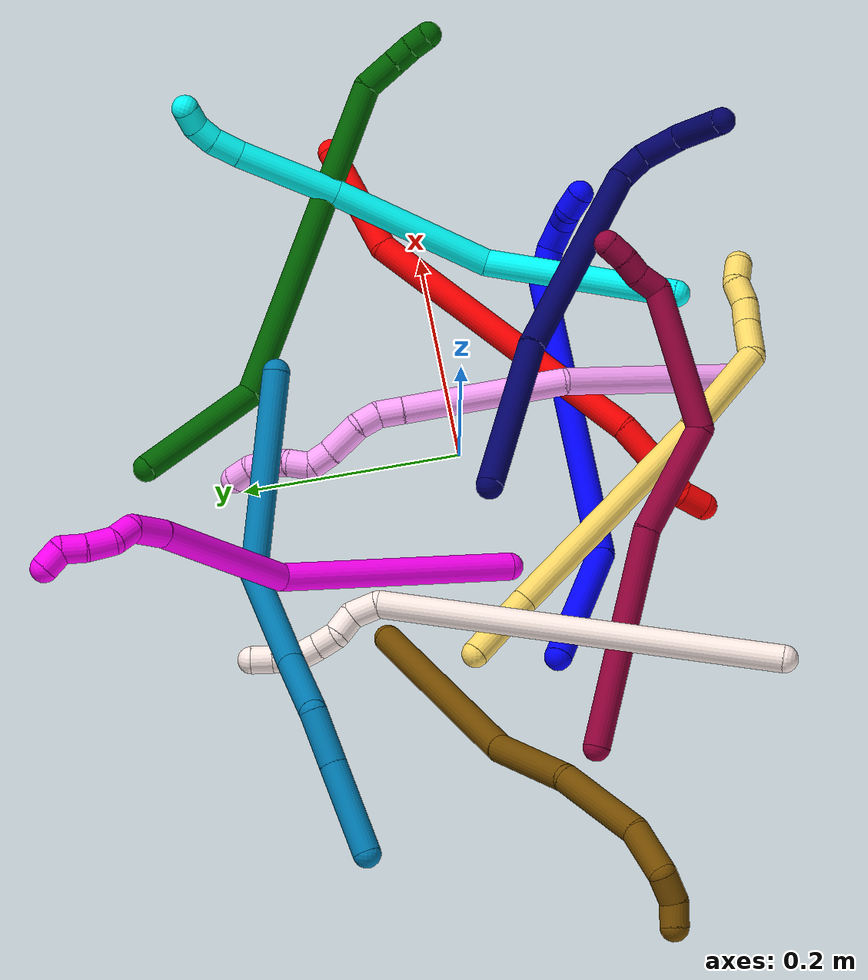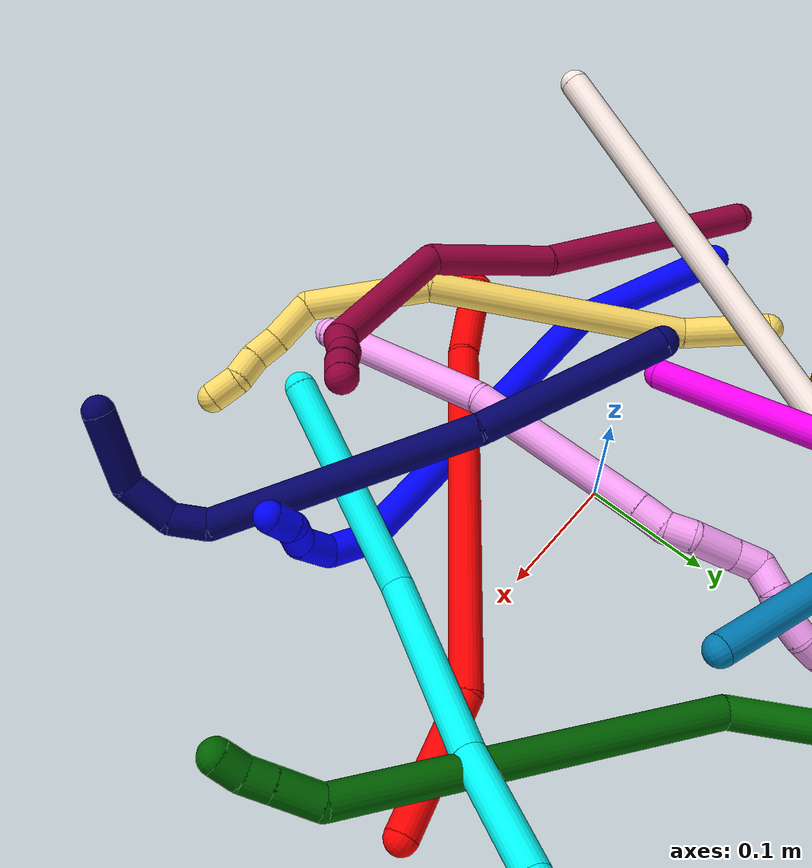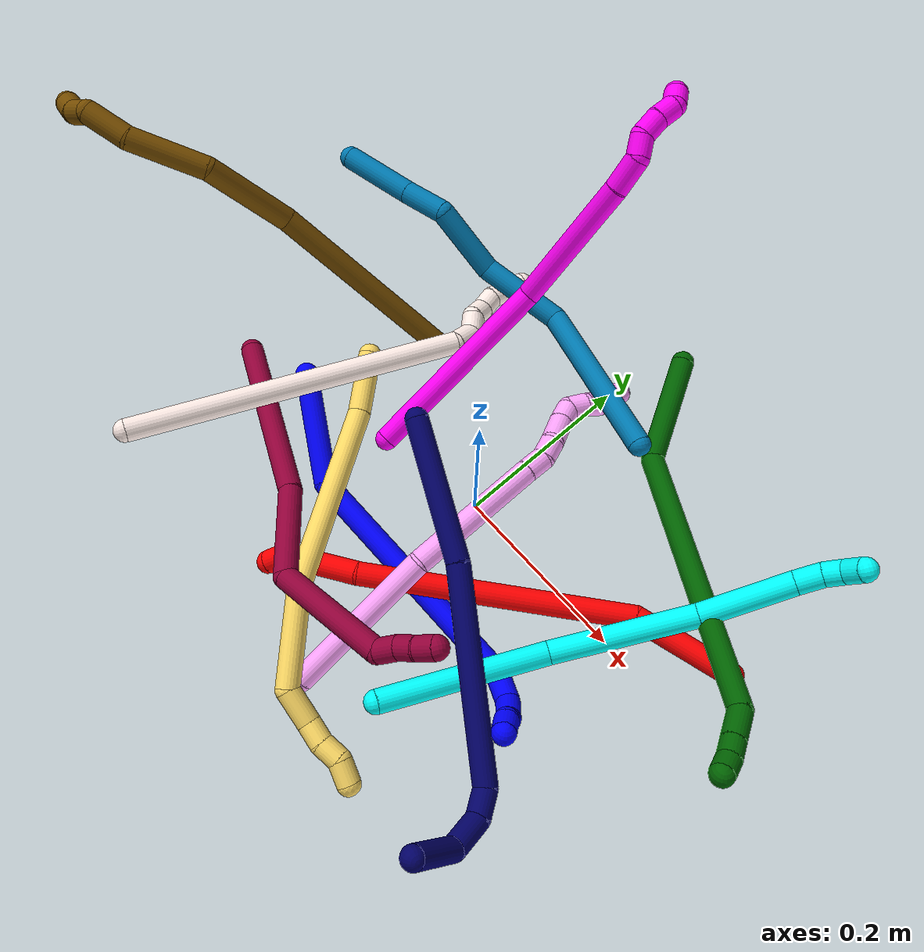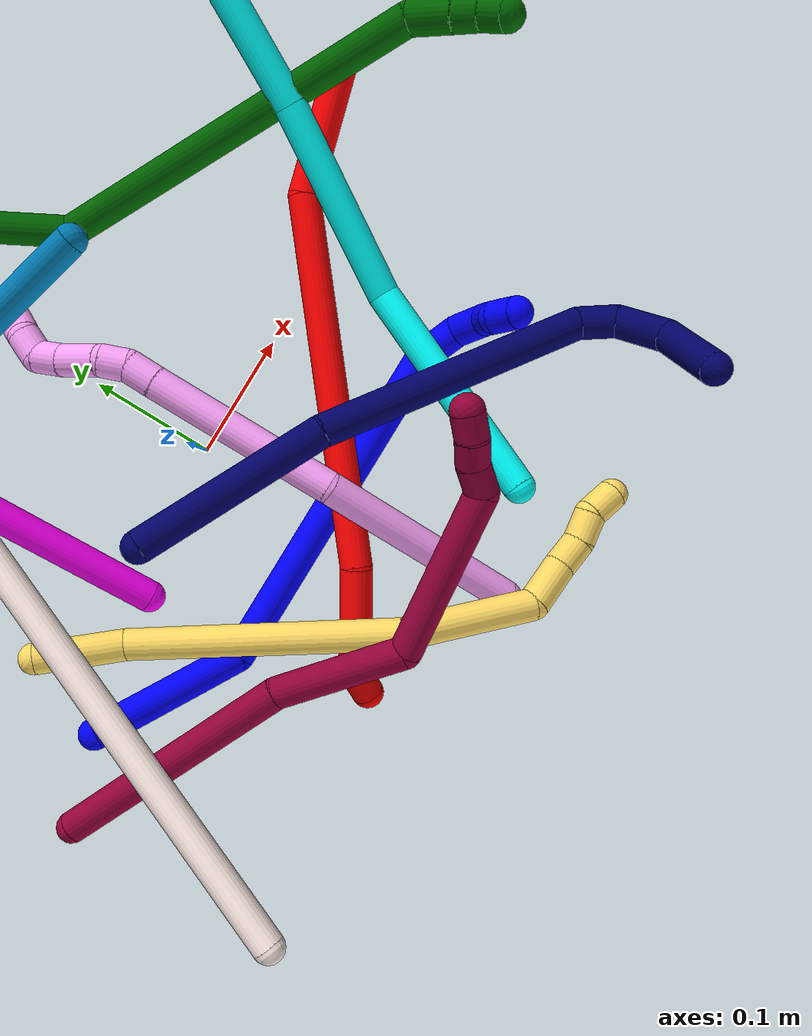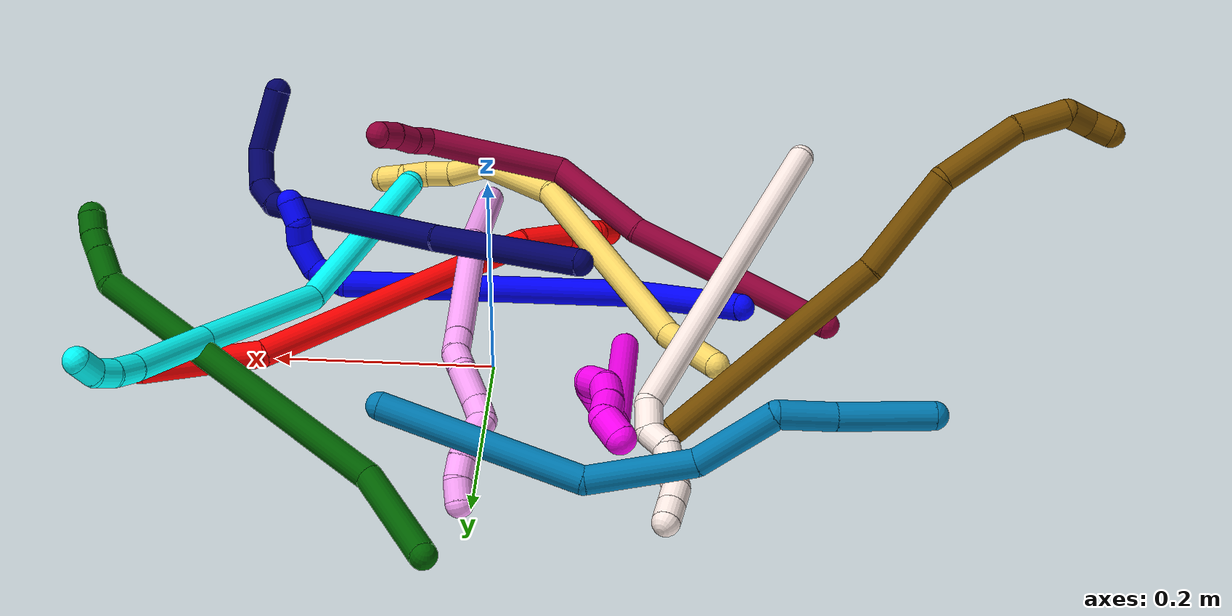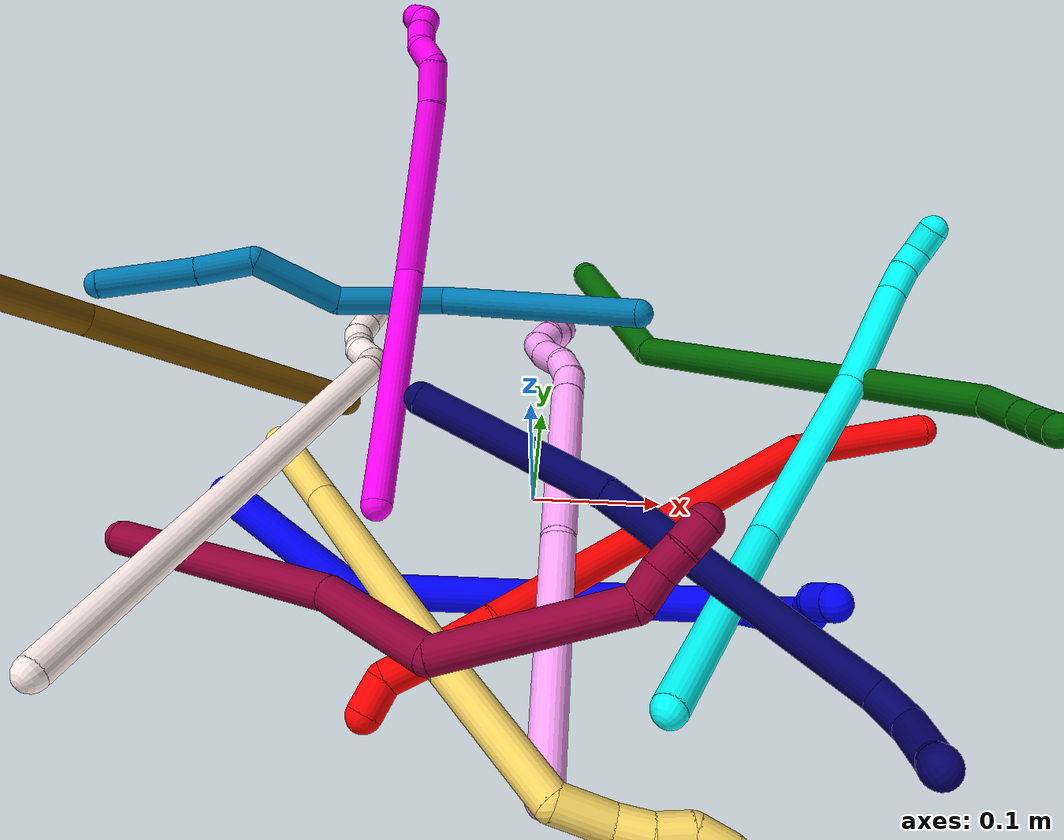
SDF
<sdf version="1.7">
 <world name="default">
  <plugin name="TubeGeneratorPlugin" filename="libtube_generator_plugin.so"/>
  <model name="photoneo_s_sensor">
   <static>1</static>
   <pose>0 0 2 1.57079 1.57079 3.14159</pose>
   <link name="link">
    <inertial><mass>0.1</mass></inertial>
    <sensor name="sensor" type="depth">
     <update_rate>30</update_rate>
     <camera>
      <horizontal_fov>1.22</horizontal_fov>
      <image><width>1920</width><height>1200</height><format>B8G8R8</format></image>
      <clip><near>0.1</near><far>4</far></clip>
      <depth_camera><output>points</output></depth_camera>
     </camera>
     <plugin name="camera_plugin" filename="libgazebo_ros_depth_camera.so">
      <baseline>0.2</baseline>
      <alwaysOn>1</alwaysOn>
      <updateRate>0.0</updateRate>
      <cameraName>camera_ir</cameraName>
      <imageTopicName>/camera/color/image_raw</imageTopicName>
      <cameraInfoTopicName>/camera/color/camera_info</cameraInfoTopicName>
      <depthImageTopicName>/camera/depth/image_raw</depthImageTopicName>
      <depthImageCameraInfoTopicName>/camera/depth/camera_info</depthImageCameraInfoTopicName>
      <pointCloudTopicName>/camera/depth/points</pointCloudTopicName>
      <frameName>fr_optical</frameName>
      <pointCloudCutoff>0.1</pointCloudCutoff>
      <pointCloudCutoffMax>2.0</pointCloudCutoffMax>
      <distortionK1>0</distortionK1>
      <distortionK2>0</distortionK2>
      <distortionK3>0</distortionK3>
      <distortionT1>0</distortionT1>
      <distortionT2>0</distortionT2>
      <CxPrime>0</CxPrime>
      <Cx>0</Cx>
      <Cy>0</Cy>
      <focalLength>0</focalLength>
      <hackBaseline>0</hackBaseline>
     </plugin>
    </sensor>
   </link>
  </model>
  <gravity>0 0 -9.8</gravity>
  <magnetic_field>6e-06 2.3e-05 -4.2e-05</magnetic_field>
  <atmosphere type="adiabatic"/>
  <physics name="default_physics" default="0" type="ode">
   <max_step_size>0.003</max_step_size>
   <real_time_factor>1</real_time_factor>
   <real_time_update_rate>1000</real_time_update_rate>
   <max_contacts>10000</max_contacts>
   <ode>
    <solver>
     <type>quick</type>
     <iters>100</iters>
     <sor>1.3</sor>
     <use_dynamic_moi_rescaling>0</use_dynamic_moi_rescaling>
    </solver>
    <constraints>
     <contact_max_correcting_vel>0</contact_max_correcting_vel>
     <contact_surface_layer>0.001</contact_surface_layer>
     <cfm>0</cfm>
     <erp>0.2</erp>
    </constraints>
   </ode>
  </physics>
  <scene><ambient>0.4 0.4 0.4 1</ambient><background>0.7 0.7 0.7 1</background><shadows>0</shadows></scene>
  <audio><device>default</device></audio>
  <spherical_coordinates>
   <surface_model>EARTH_WGS84</surface_model>
   <latitude_deg>0</latitude_deg>
   <longitude_deg>0</longitude_deg>
   <elevation>0</elevation>
   <heading_deg>0</heading_deg>
  </spherical_coordinates>
  <model name="bin">
   <static>1</static>
   <link name="bottom">
    <collision name="collision-bottom">
     <pose>0 0 -0.01 0 -0 0</pose>
     <geometry><box><size>0.8 0.6 0.02</size></box></geometry>
     <surface>
      <friction><ode><mu>100</mu><mu2>100</mu2></ode></friction>
      <contact><collide_bitmask>65535</collide_bitmask></contact>
     </surface>
    </collision>
   </link>
   <link name="west_wall">
    <collision name="collision-west_wall">
     <pose>-0.41 0 0.1 0 -0 0</pose>
     <geometry><box><size>0.02 0.6 0.2</size></box></geometry>
     <surface>
      <friction><ode><mu>100</mu><mu2>100</mu2></ode></friction>
      <contact><collide_bitmask>65535</collide_bitmask></contact>
     </surface>
    </collision>
   </link>
   <link name="east_wall">
    <collision name="collision-east_wall">
     <pose>0.41 0 0.1 0 -0 0</pose>
     <geometry><box><size>0.02 0.6 0.2</size></box></geometry>
     <surface>
      <friction><ode><mu>100</mu><mu2>100</mu2></ode></friction>
      <contact><collide_bitmask>65535</collide_bitmask></contact>
     </surface>
    </collision>
   </link>
   <link name="south_wall">
    <collision name="collision-south_wall">
     <pose>0 -0.31 0.1 0 -0 0</pose>
     <geometry><box><size>0.8 0.02 0.2</size></box></geometry>
     <surface>
      <friction><ode><mu>100</mu><mu2>100</mu2></ode></friction>
      <contact><collide_bitmask>65535</collide_bitmask></contact>
     </surface>
    </collision>
   </link>
   <link name="north_wall">
    <collision name="collision-north_wall">
     <pose>0 0.31 0.1 0 -0 0</pose>
     <geometry><box><size>0.8 0.02 0.2</size></box></geometry>
     <surface>
      <friction><ode><mu>100</mu><mu2>100</mu2></ode></friction>
      <contact><collide_bitmask>65535</collide_bitmask></contact>
     </surface>
    </collision>
   </link>
  </model>
  <model name="1">
   <static>0</static>
   <link name="1">
    <collision name="collision-cylinder-e_1_1_4">
     <pose>0.047107 0.006931 0.038579 -0.177769 0.876794 -0.083514</pose>
     <geometry><cylinder><radius>0.0125</radius><length>0.122563</length></cylinder></geometry>
     <surface>
      <friction><ode><mu>1.16</mu><mu2>1.16</mu2><slip1>0</slip1><slip2>0</slip2></ode></friction>
      <contact><ode><kp>1e+06</kp><kd>1</kd><max_vel>0</max_vel><min_depth>0.001</min_depth></ode></contact>
     </surface>
    </collision>
    <visual name="visual-cylinder-e_1_1_4">
     <pose>0.047107 0.006931 0.038579 -0.177769 0.876794 -0.083514</pose>
     <geometry><cylinder><radius>0.0125</radius><length>0.122563</length></cylinder></geometry>
     <material><ambient>0 0 1 1</ambient></material>
    </visual>
    <collision name="collision-cylinder-e_2_4_5">
     <pose>0.220745 -0.026907 0.110726 0.881973 1.17541 0.609327</pose>
     <geometry><cylinder><radius>0.0125</radius><length>0.27422</length></cylinder></geometry>
     <surface>
      <friction><ode><mu>1.16</mu><mu2>1.16</mu2><slip1>0</slip1><slip2>0</slip2></ode></friction>
      <contact><ode><kp>1e+06</kp><kd>1</kd><max_vel>0</max_vel><min_depth>0.001</min_depth></ode></contact>
     </surface>
    </collision>
    <visual name="visual-cylinder-e_2_4_5">
     <pose>0.220745 -0.026907 0.110726 0.881973 1.17541 0.609327</pose>
     <geometry><cylinder><radius>0.0125</radius><length>0.27422</length></cylinder></geometry>
     <material><ambient>0 0 1 1</ambient></material>
    </visual>
    <collision name="collision-cylinder-e_3_5_6">
     <pose>0.36348 -0.065157 0.147271 -0.702307 1.33463 -0.561995</pose>
     <geometry><cylinder><radius>0.0125</radius><length>0.033333</length></cylinder></geometry>
     <surface>
      <friction><ode><mu>1.16</mu><mu2>1.16</mu2><slip1>0</slip1><slip2>0</slip2></ode></friction>
      <contact><ode><kp>1e+06</kp><kd>1</kd><max_vel>0</max_vel><min_depth>0.001</min_depth></ode></contact>
     </surface>
    </collision>
    <visual name="visual-cylinder-e_3_5_6">
     <pose>0.36348 -0.065157 0.147271 -0.702307 1.33463 -0.561995</pose>
     <geometry><cylinder><radius>0.0125</radius><length>0.033333</length></cylinder></geometry>
     <material><ambient>0 0 1 1</ambient></material>
    </visual>
    <collision name="collision-cylinder-e_4_6_7">
     <pose>0.391347 -0.055327 0.146275 -2.06852 0.95111 -1.4273</pose>
     <geometry><cylinder><radius>0.0125</radius><length>0.028654</length></cylinder></geometry>
     <surface>
      <friction><ode><mu>1.16</mu><mu2>1.16</mu2><slip1>0</slip1><slip2>0</slip2></ode></friction>
      <contact><ode><kp>1e+06</kp><kd>1</kd><max_vel>0</max_vel><min_depth>0.001</min_depth></ode></contact>
     </surface>
    </collision>
    <visual name="visual-cylinder-e_4_6_7">
     <pose>0.391347 -0.055327 0.146275 -2.06852 0.95111 -1.4273</pose>
     <geometry><cylinder><radius>0.0125</radius><length>0.028654</length></cylinder></geometry>
     <material><ambient>0 0 1 1</ambient></material>
    </visual>
    <collision name="collision-cylinder-e_5_7_8">
     <pose>0.407182 -0.042884 0.134702 -2.54772 0.426946 -1.23275</pose>
     <geometry><cylinder><radius>0.0125</radius><length>0.020148</length></cylinder></geometry>
     <surface>
      <friction><ode><mu>1.16</mu><mu2>1.16</mu2><slip1>0</slip1><slip2>0</slip2></ode></friction>
      <contact><ode><kp>1e+06</kp><kd>1</kd><max_vel>0</max_vel><min_depth>0.001</min_depth></ode></contact>
     </surface>
    </collision>
    <visual name="visual-cylinder-e_5_7_8">
     <pose>0.407182 -0.042884 0.134702 -2.54772 0.426946 -1.23275</pose>
     <geometry><cylinder><radius>0.0125</radius><length>0.020148</length></cylinder></geometry>
     <material><ambient>0 0 1 1</ambient></material>
    </visual>
    <collision name="collision-cylinder-e_6_8_2">
     <pose>0.419088 -0.031178 0.124264 -1.97835 0.823856 -1.17305</pose>
     <geometry><cylinder><radius>0.0125</radius><length>0.021082</length></cylinder></geometry>
     <surface>
      <friction><ode><mu>1.16</mu><mu2>1.16</mu2><slip1>0</slip1><slip2>0</slip2></ode></friction>
      <contact><ode><kp>1e+06</kp><kd>1</kd><max_vel>0</max_vel><min_depth>0.001</min_depth></ode></contact>
     </surface>
    </collision>
    <visual name="visual-cylinder-e_6_8_2">
     <pose>0.419088 -0.031178 0.124264 -1.97835 0.823856 -1.17305</pose>
     <geometry><cylinder><radius>0.0125</radius><length>0.021082</length></cylinder></geometry>
     <material><ambient>0 0 1 1</ambient></material>
    </visual>
    <collision name="collision-sphere-2">
     <pose>0.426823 -0.024603 0.121426 0 -0 0</pose>
     <geometry><sphere><radius>0.0125</radius></sphere></geometry>
     <surface>
      <friction><ode><mu>1.16</mu><mu2>1.16</mu2><slip1>0</slip1><slip2>0</slip2></ode></friction>
      <contact><ode><kp>1e+06</kp><kd>1</kd><max_vel>0</max_vel><min_depth>0.001</min_depth></ode></contact>
     </surface>
    </collision>
    <visual name="visual-sphere-2">
     <pose>0.426823 -0.024603 0.121426 0 -0 0</pose>
     <geometry><sphere><radius>0.0125</radius></sphere></geometry>
     <material><ambient>0 0 1 1</ambient></material>
    </visual>
    <collision name="collision-sphere-4">
     <pose>0.094213 0.013863 0.077158 0 -0 0</pose>
     <geometry><sphere><radius>0.0125</radius></sphere></geometry>
     <surface>
      <friction><ode><mu>1.16</mu><mu2>1.16</mu2><slip1>0</slip1><slip2>0</slip2></ode></friction>
      <contact><ode><kp>1e+06</kp><kd>1</kd><max_vel>0</max_vel><min_depth>0.001</min_depth></ode></contact>
     </surface>
    </collision>
    <visual name="visual-sphere-4">
     <pose>0.094213 0.013863 0.077158 0 -0 0</pose>
     <geometry><sphere><radius>0.0125</radius></sphere></geometry>
     <material><ambient>0 0 1 1</ambient></material>
    </visual>
    <collision name="collision-sphere-1">
     <geometry><sphere><radius>0.0125</radius></sphere></geometry>
     <surface>
      <friction><ode><mu>1.16</mu><mu2>1.16</mu2><slip1>0</slip1><slip2>0</slip2></ode></friction>
      <contact><ode><kp>1e+06</kp><kd>1</kd><max_vel>0</max_vel><min_depth>0.001</min_depth></ode></contact>
     </surface>
    </collision>
    <visual name="visual-sphere-1">
     <geometry><sphere><radius>0.0125</radius></sphere></geometry>
     <material><ambient>0 0 1 1</ambient></material>
    </visual>
    <collision name="collision-sphere-8">
     <pose>0.411353 -0.037753 0.127103 0 -0 0</pose>
     <geometry><sphere><radius>0.0125</radius></sphere></geometry>
     <surface>
      <friction><ode><mu>1.16</mu><mu2>1.16</mu2><slip1>0</slip1><slip2>0</slip2></ode></friction>
      <contact><ode><kp>1e+06</kp><kd>1</kd><max_vel>0</max_vel><min_depth>0.001</min_depth></ode></contact>
     </surface>
    </collision>
    <visual name="visual-sphere-8">
     <pose>0.411353 -0.037753 0.127103 0 -0 0</pose>
     <geometry><sphere><radius>0.0125</radius></sphere></geometry>
     <material><ambient>0 0 1 1</ambient></material>
    </visual>
    <collision name="collision-sphere-5">
     <pose>0.347276 -0.067676 0.144294 0 -0 0</pose>
     <geometry><sphere><radius>0.0125</radius></sphere></geometry>
     <surface>
      <friction><ode><mu>1.16</mu><mu2>1.16</mu2><slip1>0</slip1><slip2>0</slip2></ode></friction>
      <contact><ode><kp>1e+06</kp><kd>1</kd><max_vel>0</max_vel><min_depth>0.001</min_depth></ode></contact>
     </surface>
    </collision>
    <visual name="visual-sphere-5">
     <pose>0.347276 -0.067676 0.144294 0 -0 0</pose>
     <geometry><sphere><radius>0.0125</radius></sphere></geometry>
     <material><ambient>0 0 1 1</ambient></material>
    </visual>
    <collision name="collision-sphere-6">
     <pose>0.379684 -0.062638 0.150247 0 -0 0</pose>
     <geometry><sphere><radius>0.0125</radius></sphere></geometry>
     <surface>
      <friction><ode><mu>1.16</mu><mu2>1.16</mu2><slip1>0</slip1><slip2>0</slip2></ode></friction>
      <contact><ode><kp>1e+06</kp><kd>1</kd><max_vel>0</max_vel><min_depth>0.001</min_depth></ode></contact>
     </surface>
    </collision>
    <visual name="visual-sphere-6">
     <pose>0.379684 -0.062638 0.150247 0 -0 0</pose>
     <geometry><sphere><radius>0.0125</radius></sphere></geometry>
     <material><ambient>0 0 1 1</ambient></material>
    </visual>
    <collision name="collision-sphere-7">
     <pose>0.40301 -0.048015 0.142302 0 -0 0</pose>
     <geometry><sphere><radius>0.0125</radius></sphere></geometry>
     <surface>
      <friction><ode><mu>1.16</mu><mu2>1.16</mu2><slip1>0</slip1><slip2>0</slip2></ode></friction>
      <contact><ode><kp>1e+06</kp><kd>1</kd><max_vel>0</max_vel><min_depth>0.001</min_depth></ode></contact>
     </surface>
    </collision>
    <visual name="visual-sphere-7">
     <pose>0.40301 -0.048015 0.142302 0 -0 0</pose>
     <geometry><sphere><radius>0.0125</radius></sphere></geometry>
     <material><ambient>0 0 1 1</ambient></material>
    </visual>
    <inertial>
     <pose>0.21335 -0.023615 0.099051 0 -0 0</pose>
     <mass>0.5</mass>
     <inertia>
      <ixx>0.00105</ixx>
      <ixy>0</ixy>
      <ixz>0</ixz>
      <iyy>0.002136</iyy>
      <iyz>0</iyz>
      <izz>-0.001224</izz>
     </inertia>
    </inertial>
   </link>
   <pose>-0.224699 -0.046799 0.043537 2.79501 -0.34463 -0.195182</pose>
  </model>
  <model name="2">
   <static>0</static>
   <link name="2">
    <collision name="collision-cylinder-e_1_1_4">
     <pose>-0.031927 -0.04395 -0.003594 1.65238 -0.626674 -0.676175</pose>
     <geometry><cylinder><radius>0.0125</radius><length>0.108882</length></cylinder></geometry>
     <surface>
      <friction><ode><mu>1.16</mu><mu2>1.16</mu2><slip1>0</slip1><slip2>0</slip2></ode></friction>
      <contact><ode><kp>1e+06</kp><kd>1</kd><max_vel>0</max_vel><min_depth>0.001</min_depth></ode></contact>
     </surface>
    </collision>
    <visual name="visual-cylinder-e_1_1_4">
     <pose>-0.031927 -0.04395 -0.003594 1.65238 -0.626674 -0.676175</pose>
     <geometry><cylinder><radius>0.0125</radius><length>0.108882</length></cylinder></geometry>
     <material><ambient>1 0 0 1</ambient></material>
    </visual>
    <collision name="collision-cylinder-e_2_4_5">
     <pose>-0.16039 -0.175368 -0.066866 2.16954 -0.739227 -1.2655</pose>
     <geometry><cylinder><radius>0.0125</radius><length>0.286575</length></cylinder></geometry>
     <surface>
      <friction><ode><mu>1.16</mu><mu2>1.16</mu2><slip1>0</slip1><slip2>0</slip2></ode></friction>
      <contact><ode><kp>1e+06</kp><kd>1</kd><max_vel>0</max_vel><min_depth>0.001</min_depth></ode></contact>
     </surface>
    </collision>
    <visual name="visual-cylinder-e_2_4_5">
     <pose>-0.16039 -0.175368 -0.066866 2.16954 -0.739227 -1.2655</pose>
     <geometry><cylinder><radius>0.0125</radius><length>0.286575</length></cylinder></geometry>
     <material><ambient>1 0 0 1</ambient></material>
    </visual>
    <collision name="collision-cylinder-e_3_5_6">
     <pose>-0.275736 -0.277236 -0.13136 1.89344 -0.891699 -1.17195</pose>
     <geometry><cylinder><radius>0.0125</radius><length>0.048349</length></cylinder></geometry>
     <surface>
      <friction><ode><mu>1.16</mu><mu2>1.16</mu2><slip1>0</slip1><slip2>0</slip2></ode></friction>
      <contact><ode><kp>1e+06</kp><kd>1</kd><max_vel>0</max_vel><min_depth>0.001</min_depth></ode></contact>
     </surface>
    </collision>
    <visual name="visual-cylinder-e_3_5_6">
     <pose>-0.275736 -0.277236 -0.13136 1.89344 -0.891699 -1.17195</pose>
     <geometry><cylinder><radius>0.0125</radius><length>0.048349</length></cylinder></geometry>
     <material><ambient>1 0 0 1</ambient></material>
    </visual>
    <collision name="collision-cylinder-e_4_6_7">
     <pose>-0.306705 -0.301524 -0.138783 1.82873 -0.871475 -1.0872</pose>
     <geometry><cylinder><radius>0.0125</radius><length>0.031773</length></cylinder></geometry>
     <surface>
      <friction><ode><mu>1.16</mu><mu2>1.16</mu2><slip1>0</slip1><slip2>0</slip2></ode></friction>
      <contact><ode><kp>1e+06</kp><kd>1</kd><max_vel>0</max_vel><min_depth>0.001</min_depth></ode></contact>
     </surface>
    </collision>
    <visual name="visual-cylinder-e_4_6_7">
     <pose>-0.306705 -0.301524 -0.138783 1.82873 -0.871475 -1.0872</pose>
     <geometry><cylinder><radius>0.0125</radius><length>0.031773</length></cylinder></geometry>
     <material><ambient>1 0 0 1</ambient></material>
    </visual>
    <collision name="collision-cylinder-e_5_7_2">
     <pose>-0.330311 -0.312167 -0.14557 2.96296 -1.21562 -2.88554</pose>
     <geometry><cylinder><radius>0.0125</radius><length>0.02442</length></cylinder></geometry>
     <surface>
      <friction><ode><mu>1.16</mu><mu2>1.16</mu2><slip1>0</slip1><slip2>0</slip2></ode></friction>
      <contact><ode><kp>1e+06</kp><kd>1</kd><max_vel>0</max_vel><min_depth>0.001</min_depth></ode></contact>
     </surface>
    </collision>
    <visual name="visual-cylinder-e_5_7_2">
     <pose>-0.330311 -0.312167 -0.14557 2.96296 -1.21562 -2.88554</pose>
     <geometry><cylinder><radius>0.0125</radius><length>0.02442</length></cylinder></geometry>
     <material><ambient>1 0 0 1</ambient></material>
    </visual>
    <collision name="collision-sphere-2">
     <pose>-0.341759 -0.312921 -0.149748 0 -0 0</pose>
     <geometry><sphere><radius>0.0125</radius></sphere></geometry>
     <surface>
      <friction><ode><mu>1.16</mu><mu2>1.16</mu2><slip1>0</slip1><slip2>0</slip2></ode></friction>
      <contact><ode><kp>1e+06</kp><kd>1</kd><max_vel>0</max_vel><min_depth>0.001</min_depth></ode></contact>
     </surface>
    </collision>
    <visual name="visual-sphere-2">
     <pose>-0.341759 -0.312921 -0.149748 0 -0 0</pose>
     <geometry><sphere><radius>0.0125</radius></sphere></geometry>
     <material><ambient>1 0 0 1</ambient></material>
    </visual>
    <collision name="collision-sphere-7">
     <pose>-0.318863 -0.311412 -0.141391 0 -0 0</pose>
     <geometry><sphere><radius>0.0125</radius></sphere></geometry>
     <surface>
      <friction><ode><mu>1.16</mu><mu2>1.16</mu2><slip1>0</slip1><slip2>0</slip2></ode></friction>
      <contact><ode><kp>1e+06</kp><kd>1</kd><max_vel>0</max_vel><min_depth>0.001</min_depth></ode></contact>
     </surface>
    </collision>
    <visual name="visual-sphere-7">
     <pose>-0.318863 -0.311412 -0.141391 0 -0 0</pose>
     <geometry><sphere><radius>0.0125</radius></sphere></geometry>
     <material><ambient>1 0 0 1</ambient></material>
    </visual>
    <collision name="collision-sphere-6">
     <pose>-0.294547 -0.291637 -0.136174 0 -0 0</pose>
     <geometry><sphere><radius>0.0125</radius></sphere></geometry>
     <surface>
      <friction><ode><mu>1.16</mu><mu2>1.16</mu2><slip1>0</slip1><slip2>0</slip2></ode></friction>
      <contact><ode><kp>1e+06</kp><kd>1</kd><max_vel>0</max_vel><min_depth>0.001</min_depth></ode></contact>
     </surface>
    </collision>
    <visual name="visual-sphere-6">
     <pose>-0.294547 -0.291637 -0.136174 0 -0 0</pose>
     <geometry><sphere><radius>0.0125</radius></sphere></geometry>
     <material><ambient>1 0 0 1</ambient></material>
    </visual>
    <collision name="collision-sphere-5">
     <pose>-0.256925 -0.262836 -0.126545 0 -0 0</pose>
     <geometry><sphere><radius>0.0125</radius></sphere></geometry>
     <surface>
      <friction><ode><mu>1.16</mu><mu2>1.16</mu2><slip1>0</slip1><slip2>0</slip2></ode></friction>
      <contact><ode><kp>1e+06</kp><kd>1</kd><max_vel>0</max_vel><min_depth>0.001</min_depth></ode></contact>
     </surface>
    </collision>
    <visual name="visual-sphere-5">
     <pose>-0.256925 -0.262836 -0.126545 0 -0 0</pose>
     <geometry><sphere><radius>0.0125</radius></sphere></geometry>
     <material><ambient>1 0 0 1</ambient></material>
    </visual>
    <collision name="collision-sphere-1">
     <geometry><sphere><radius>0.0125</radius></sphere></geometry>
     <surface>
      <friction><ode><mu>1.16</mu><mu2>1.16</mu2><slip1>0</slip1><slip2>0</slip2></ode></friction>
      <contact><ode><kp>1e+06</kp><kd>1</kd><max_vel>0</max_vel><min_depth>0.001</min_depth></ode></contact>
     </surface>
    </collision>
    <visual name="visual-sphere-1">
     <geometry><sphere><radius>0.0125</radius></sphere></geometry>
     <material><ambient>1 0 0 1</ambient></material>
    </visual>
    <collision name="collision-sphere-4">
     <pose>-0.063854 -0.087899 -0.007188 0 -0 0</pose>
     <geometry><sphere><radius>0.0125</radius></sphere></geometry>
     <surface>
      <friction><ode><mu>1.16</mu><mu2>1.16</mu2><slip1>0</slip1><slip2>0</slip2></ode></friction>
      <contact><ode><kp>1e+06</kp><kd>1</kd><max_vel>0</max_vel><min_depth>0.001</min_depth></ode></contact>
     </surface>
    </collision>
    <visual name="visual-sphere-4">
     <pose>-0.063854 -0.087899 -0.007188 0 -0 0</pose>
     <geometry><sphere><radius>0.0125</radius></sphere></geometry>
     <material><ambient>1 0 0 1</ambient></material>
    </visual>
    <inertial>
     <pose>-0.161166 -0.171298 -0.067738 0 -0 0</pose>
     <mass>0.5</mass>
     <inertia>
      <ixx>-0.000971</ixx>
      <ixy>0</ixy>
      <ixz>0</ixz>
      <iyy>-0.000723</iyy>
      <iyz>0</iyz>
      <izz>0.0027</izz>
     </inertia>
    </inertial>
   </link>
   <pose>0.310083 0.063931 0.030777 -2.376 -0.800247 0.844855</pose>
  </model>
  <model name="3">
   <static>0</static>
   <link name="3">
    <collision name="collision-cylinder-e_1_1_4">
     <pose>0.016316 0.017245 0.08682 -0.196077 0.18228 -0.017977</pose>
     <geometry><cylinder><radius>0.0125</radius><length>0.180016</length></cylinder></geometry>
     <surface>
      <friction><ode><mu>1.16</mu><mu2>1.16</mu2><slip1>0</slip1><slip2>0</slip2></ode></friction>
      <contact><ode><kp>1e+06</kp><kd>1</kd><max_vel>0</max_vel><min_depth>0.001</min_depth></ode></contact>
     </surface>
    </collision>
    <visual name="visual-cylinder-e_1_1_4">
     <pose>0.016316 0.017245 0.08682 -0.196077 0.18228 -0.017977</pose>
     <geometry><cylinder><radius>0.0125</radius><length>0.180016</length></cylinder></geometry>
     <material><ambient>0.003922 1 0.996078 1</ambient></material>
    </visual>
    <collision name="collision-cylinder-e_2_4_5">
     <pose>0.023738 0.026837 0.249365 0.10072 -0.116327 -0.00587</pose>
     <geometry><cylinder><radius>0.0125</radius><length>0.153254</length></cylinder></geometry>
     <surface>
      <friction><ode><mu>1.16</mu><mu2>1.16</mu2><slip1>0</slip1><slip2>0</slip2></ode></friction>
      <contact><ode><kp>1e+06</kp><kd>1</kd><max_vel>0</max_vel><min_depth>0.001</min_depth></ode></contact>
     </surface>
    </collision>
    <visual name="visual-cylinder-e_2_4_5">
     <pose>0.023738 0.026837 0.249365 0.10072 -0.116327 -0.00587</pose>
     <geometry><cylinder><radius>0.0125</radius><length>0.153254</length></cylinder></geometry>
     <material><ambient>0.003922 1 0.996078 1</ambient></material>
    </visual>
    <collision name="collision-cylinder-e_3_5_6">
     <pose>0.006036 0.016643 0.372626 0.053424 -0.182962 -0.004902</pose>
     <geometry><cylinder><radius>0.0125</radius><length>0.096829</length></cylinder></geometry>
     <surface>
      <friction><ode><mu>1.16</mu><mu2>1.16</mu2><slip1>0</slip1><slip2>0</slip2></ode></friction>
      <contact><ode><kp>1e+06</kp><kd>1</kd><max_vel>0</max_vel><min_depth>0.001</min_depth></ode></contact>
     </surface>
    </collision>
    <visual name="visual-cylinder-e_3_5_6">
     <pose>0.006036 0.016643 0.372626 0.053424 -0.182962 -0.004902</pose>
     <geometry><cylinder><radius>0.0125</radius><length>0.096829</length></cylinder></geometry>
     <material><ambient>0.003922 1 0.996078 1</ambient></material>
    </visual>
    <collision name="collision-cylinder-e_4_6_7">
     <pose>-0.005766 0.012247 0.433403 0.13908 -0.220312 -0.015407</pose>
     <geometry><cylinder><radius>0.0125</radius><length>0.027398</length></cylinder></geometry>
     <surface>
      <friction><ode><mu>1.16</mu><mu2>1.16</mu2><slip1>0</slip1><slip2>0</slip2></ode></friction>
      <contact><ode><kp>1e+06</kp><kd>1</kd><max_vel>0</max_vel><min_depth>0.001</min_depth></ode></contact>
     </surface>
    </collision>
    <visual name="visual-cylinder-e_4_6_7">
     <pose>-0.005766 0.012247 0.433403 0.13908 -0.220312 -0.015407</pose>
     <geometry><cylinder><radius>0.0125</radius><length>0.027398</length></cylinder></geometry>
     <material><ambient>0.003922 1 0.996078 1</ambient></material>
    </visual>
    <collision name="collision-cylinder-e_5_7_8">
     <pose>-0.011121 0.006761 0.455954 0.372032 -0.231921 -0.043835</pose>
     <geometry><cylinder><radius>0.0125</radius><length>0.020541</length></cylinder></geometry>
     <surface>
      <friction><ode><mu>1.16</mu><mu2>1.16</mu2><slip1>0</slip1><slip2>0</slip2></ode></friction>
      <contact><ode><kp>1e+06</kp><kd>1</kd><max_vel>0</max_vel><min_depth>0.001</min_depth></ode></contact>
     </surface>
    </collision>
    <visual name="visual-cylinder-e_5_7_8">
     <pose>-0.011121 0.006761 0.455954 0.372032 -0.231921 -0.043835</pose>
     <geometry><cylinder><radius>0.0125</radius><length>0.020541</length></cylinder></geometry>
     <material><ambient>0.003922 1 0.996078 1</ambient></material>
    </visual>
    <collision name="collision-cylinder-e_6_8_2">
     <pose>-0.019075 -0.00346 0.472041 0.771345 -0.534485 -0.221413</pose>
     <geometry><cylinder><radius>0.0125</radius><length>0.021962</length></cylinder></geometry>
     <surface>
      <friction><ode><mu>1.16</mu><mu2>1.16</mu2><slip1>0</slip1><slip2>0</slip2></ode></friction>
      <contact><ode><kp>1e+06</kp><kd>1</kd><max_vel>0</max_vel><min_depth>0.001</min_depth></ode></contact>
     </surface>
    </collision>
    <visual name="visual-cylinder-e_6_8_2">
     <pose>-0.019075 -0.00346 0.472041 0.771345 -0.534485 -0.221413</pose>
     <geometry><cylinder><radius>0.0125</radius><length>0.021962</length></cylinder></geometry>
     <material><ambient>0.003922 1 0.996078 1</ambient></material>
    </visual>
    <collision name="collision-sphere-2">
     <pose>-0.024669 -0.010048 0.478816 0 -0 0</pose>
     <geometry><sphere><radius>0.0125</radius></sphere></geometry>
     <surface>
      <friction><ode><mu>1.16</mu><mu2>1.16</mu2><slip1>0</slip1><slip2>0</slip2></ode></friction>
      <contact><ode><kp>1e+06</kp><kd>1</kd><max_vel>0</max_vel><min_depth>0.001</min_depth></ode></contact>
     </surface>
    </collision>
    <visual name="visual-sphere-2">
     <pose>-0.024669 -0.010048 0.478816 0 -0 0</pose>
     <geometry><sphere><radius>0.0125</radius></sphere></geometry>
     <material><ambient>0.003922 1 0.996078 1</ambient></material>
    </visual>
    <collision name="collision-sphere-4">
     <pose>0.032632 0.03449 0.173641 0 -0 0</pose>
     <geometry><sphere><radius>0.0125</radius></sphere></geometry>
     <surface>
      <friction><ode><mu>1.16</mu><mu2>1.16</mu2><slip1>0</slip1><slip2>0</slip2></ode></friction>
      <contact><ode><kp>1e+06</kp><kd>1</kd><max_vel>0</max_vel><min_depth>0.001</min_depth></ode></contact>
     </surface>
    </collision>
    <visual name="visual-sphere-4">
     <pose>0.032632 0.03449 0.173641 0 -0 0</pose>
     <geometry><sphere><radius>0.0125</radius></sphere></geometry>
     <material><ambient>0.003922 1 0.996078 1</ambient></material>
    </visual>
    <collision name="collision-sphere-1">
     <geometry><sphere><radius>0.0125</radius></sphere></geometry>
     <surface>
      <friction><ode><mu>1.16</mu><mu2>1.16</mu2><slip1>0</slip1><slip2>0</slip2></ode></friction>
      <contact><ode><kp>1e+06</kp><kd>1</kd><max_vel>0</max_vel><min_depth>0.001</min_depth></ode></contact>
     </surface>
    </collision>
    <visual name="visual-sphere-1">
     <geometry><sphere><radius>0.0125</radius></sphere></geometry>
     <material><ambient>0.003922 1 0.996078 1</ambient></material>
    </visual>
    <collision name="collision-sphere-8">
     <pose>-0.013482 0.003127 0.465266 0 -0 0</pose>
     <geometry><sphere><radius>0.0125</radius></sphere></geometry>
     <surface>
      <friction><ode><mu>1.16</mu><mu2>1.16</mu2><slip1>0</slip1><slip2>0</slip2></ode></friction>
      <contact><ode><kp>1e+06</kp><kd>1</kd><max_vel>0</max_vel><min_depth>0.001</min_depth></ode></contact>
     </surface>
    </collision>
    <visual name="visual-sphere-8">
     <pose>-0.013482 0.003127 0.465266 0 -0 0</pose>
     <geometry><sphere><radius>0.0125</radius></sphere></geometry>
     <material><ambient>0.003922 1 0.996078 1</ambient></material>
    </visual>
    <collision name="collision-sphere-5">
     <pose>0.014844 0.019185 0.325088 0 -0 0</pose>
     <geometry><sphere><radius>0.0125</radius></sphere></geometry>
     <surface>
      <friction><ode><mu>1.16</mu><mu2>1.16</mu2><slip1>0</slip1><slip2>0</slip2></ode></friction>
      <contact><ode><kp>1e+06</kp><kd>1</kd><max_vel>0</max_vel><min_depth>0.001</min_depth></ode></contact>
     </surface>
    </collision>
    <visual name="visual-sphere-5">
     <pose>0.014844 0.019185 0.325088 0 -0 0</pose>
     <geometry><sphere><radius>0.0125</radius></sphere></geometry>
     <material><ambient>0.003922 1 0.996078 1</ambient></material>
    </visual>
    <collision name="collision-sphere-6">
     <pose>-0.002773 0.0141 0.420165 0 -0 0</pose>
     <geometry><sphere><radius>0.0125</radius></sphere></geometry>
     <surface>
      <friction><ode><mu>1.16</mu><mu2>1.16</mu2><slip1>0</slip1><slip2>0</slip2></ode></friction>
      <contact><ode><kp>1e+06</kp><kd>1</kd><max_vel>0</max_vel><min_depth>0.001</min_depth></ode></contact>
     </surface>
    </collision>
    <visual name="visual-sphere-6">
     <pose>-0.002773 0.0141 0.420165 0 -0 0</pose>
     <geometry><sphere><radius>0.0125</radius></sphere></geometry>
     <material><ambient>0.003922 1 0.996078 1</ambient></material>
    </visual>
    <collision name="collision-sphere-7">
     <pose>-0.00876 0.010394 0.446642 0 -0 0</pose>
     <geometry><sphere><radius>0.0125</radius></sphere></geometry>
     <surface>
      <friction><ode><mu>1.16</mu><mu2>1.16</mu2><slip1>0</slip1><slip2>0</slip2></ode></friction>
      <contact><ode><kp>1e+06</kp><kd>1</kd><max_vel>0</max_vel><min_depth>0.001</min_depth></ode></contact>
     </surface>
    </collision>
    <visual name="visual-sphere-7">
     <pose>-0.00876 0.010394 0.446642 0 -0 0</pose>
     <geometry><sphere><radius>0.0125</radius></sphere></geometry>
     <material><ambient>0.003922 1 0.996078 1</ambient></material>
    </visual>
    <inertial>
     <pose>0.012708 0.018454 0.243067 0 -0 0</pose>
     <mass>0.5</mass>
     <inertia>
      <ixx>0.000859</ixx>
      <ixy>0</ixy>
      <ixz>0</ixz>
      <iyy>0.000861</iyy>
      <iyz>0</iyz>
      <izz>-5.8e-05</izz>
     </inertia>
    </inertial>
   </link>
   <pose>0.100868 -0.220407 0.052137 -1.30751 1.0601 -0.270111</pose>
  </model>
  <model name="4">
   <static>0</static>
   <link name="4">
    <collision name="collision-cylinder-e_1_1_4">
     <pose>0.023287 0.079418 0.016361 -1.36763 0.279662 -0.228419</pose>
     <geometry><cylinder><radius>0.0125</radius><length>0.168727</length></cylinder></geometry>
     <surface>
      <friction><ode><mu>1.16</mu><mu2>1.16</mu2><slip1>0</slip1><slip2>0</slip2></ode></friction>
      <contact><ode><kp>1e+06</kp><kd>1</kd><max_vel>0</max_vel><min_depth>0.001</min_depth></ode></contact>
     </surface>
    </collision>
    <visual name="visual-cylinder-e_1_1_4">
     <pose>0.023287 0.079418 0.016361 -1.36763 0.279662 -0.228419</pose>
     <geometry><cylinder><radius>0.0125</radius><length>0.168727</length></cylinder></geometry>
     <material><ambient>1 0.65098 0.996078 1</ambient></material>
    </visual>
    <collision name="collision-cylinder-e_2_4_5">
     <pose>0.043236 0.232916 0.039133 -1.48448 -0.044857 0.041144</pose>
     <geometry><cylinder><radius>0.0125</radius><length>0.148862</length></cylinder></geometry>
     <surface>
      <friction><ode><mu>1.16</mu><mu2>1.16</mu2><slip1>0</slip1><slip2>0</slip2></ode></friction>
      <contact><ode><kp>1e+06</kp><kd>1</kd><max_vel>0</max_vel><min_depth>0.001</min_depth></ode></contact>
     </surface>
    </collision>
    <visual name="visual-cylinder-e_2_4_5">
     <pose>0.043236 0.232916 0.039133 -1.48448 -0.044857 0.041144</pose>
     <geometry><cylinder><radius>0.0125</radius><length>0.148862</length></cylinder></geometry>
     <material><ambient>1 0.65098 0.996078 1</ambient></material>
    </visual>
    <collision name="collision-cylinder-e_3_5_6">
     <pose>0.038937 0.31847 0.046108 -1.5216 -0.083483 0.079478</pose>
     <geometry><cylinder><radius>0.0125</radius><length>0.023058</length></cylinder></geometry>
     <surface>
      <friction><ode><mu>1.16</mu><mu2>1.16</mu2><slip1>0</slip1><slip2>0</slip2></ode></friction>
      <contact><ode><kp>1e+06</kp><kd>1</kd><max_vel>0</max_vel><min_depth>0.001</min_depth></ode></contact>
     </surface>
    </collision>
    <visual name="visual-cylinder-e_3_5_6">
     <pose>0.038937 0.31847 0.046108 -1.5216 -0.083483 0.079478</pose>
     <geometry><cylinder><radius>0.0125</radius><length>0.023058</length></cylinder></geometry>
     <material><ambient>1 0.65098 0.996078 1</ambient></material>
    </visual>
    <collision name="collision-cylinder-e_4_6_7">
     <pose>0.035747 0.339521 0.050712 -1.17165 -0.211276 0.140479</pose>
     <geometry><cylinder><radius>0.0125</radius><length>0.021258</length></cylinder></geometry>
     <surface>
      <friction><ode><mu>1.16</mu><mu2>1.16</mu2><slip1>0</slip1><slip2>0</slip2></ode></friction>
      <contact><ode><kp>1e+06</kp><kd>1</kd><max_vel>0</max_vel><min_depth>0.001</min_depth></ode></contact>
     </surface>
    </collision>
    <visual name="visual-cylinder-e_4_6_7">
     <pose>0.035747 0.339521 0.050712 -1.17165 -0.211276 0.140479</pose>
     <geometry><cylinder><radius>0.0125</radius><length>0.021258</length></cylinder></geometry>
     <material><ambient>1 0.65098 0.996078 1</ambient></material>
    </visual>
    <collision name="collision-cylinder-e_5_7_8">
     <pose>0.023451 0.362197 0.060134 -1.18092 -0.617891 0.421473</pose>
     <geometry><cylinder><radius>0.0125</radius><length>0.034753</length></cylinder></geometry>
     <surface>
      <friction><ode><mu>1.16</mu><mu2>1.16</mu2><slip1>0</slip1><slip2>0</slip2></ode></friction>
      <contact><ode><kp>1e+06</kp><kd>1</kd><max_vel>0</max_vel><min_depth>0.001</min_depth></ode></contact>
     </surface>
    </collision>
    <visual name="visual-cylinder-e_5_7_8">
     <pose>0.023451 0.362197 0.060134 -1.18092 -0.617891 0.421473</pose>
     <geometry><cylinder><radius>0.0125</radius><length>0.034753</length></cylinder></geometry>
     <material><ambient>1 0.65098 0.996078 1</ambient></material>
    </visual>
    <collision name="collision-cylinder-e_6_8_9">
     <pose>0.009271 0.384551 0.068988 -1.2119 -0.394426 0.27515</pose>
     <geometry><cylinder><radius>0.0125</radius><length>0.021411</length></cylinder></geometry>
     <surface>
      <friction><ode><mu>1.16</mu><mu2>1.16</mu2><slip1>0</slip1><slip2>0</slip2></ode></friction>
      <contact><ode><kp>1e+06</kp><kd>1</kd><max_vel>0</max_vel><min_depth>0.001</min_depth></ode></contact>
     </surface>
    </collision>
    <visual name="visual-cylinder-e_6_8_9">
     <pose>0.009271 0.384551 0.068988 -1.2119 -0.394426 0.27515</pose>
     <geometry><cylinder><radius>0.0125</radius><length>0.021411</length></cylinder></geometry>
     <material><ambient>1 0.65098 0.996078 1</ambient></material>
    </visual>
    <collision name="collision-cylinder-e_7_9_10">
     <pose>0.004616 0.403391 0.068846 -1.93133 -0.052811 0.076331</pose>
     <geometry><cylinder><radius>0.0125</radius><length>0.020517</length></cylinder></geometry>
     <surface>
      <friction><ode><mu>1.16</mu><mu2>1.16</mu2><slip1>0</slip1><slip2>0</slip2></ode></friction>
      <contact><ode><kp>1e+06</kp><kd>1</kd><max_vel>0</max_vel><min_depth>0.001</min_depth></ode></contact>
     </surface>
    </collision>
    <visual name="visual-cylinder-e_7_9_10">
     <pose>0.004616 0.403391 0.068846 -1.93133 -0.052811 0.076331</pose>
     <geometry><cylinder><radius>0.0125</radius><length>0.020517</length></cylinder></geometry>
     <material><ambient>1 0.65098 0.996078 1</ambient></material>
    </visual>
    <collision name="collision-cylinder-e_8_10_11">
     <pose>-0.000211 0.421287 0.060644 -2.07524 -0.423996 0.699386</pose>
     <geometry><cylinder><radius>0.0125</radius><length>0.020831</length></cylinder></geometry>
     <surface>
      <friction><ode><mu>1.16</mu><mu2>1.16</mu2><slip1>0</slip1><slip2>0</slip2></ode></friction>
      <contact><ode><kp>1e+06</kp><kd>1</kd><max_vel>0</max_vel><min_depth>0.001</min_depth></ode></contact>
     </surface>
    </collision>
    <visual name="visual-cylinder-e_8_10_11">
     <pose>-0.000211 0.421287 0.060644 -2.07524 -0.423996 0.699386</pose>
     <geometry><cylinder><radius>0.0125</radius><length>0.020831</length></cylinder></geometry>
     <material><ambient>1 0.65098 0.996078 1</ambient></material>
    </visual>
    <collision name="collision-cylinder-e_9_11_12">
     <pose>-0.008728 0.438624 0.054173 -1.77642 -0.43033 0.525252</pose>
     <geometry><cylinder><radius>0.0125</radius><length>0.020291</length></cylinder></geometry>
     <surface>
      <friction><ode><mu>1.16</mu><mu2>1.16</mu2><slip1>0</slip1><slip2>0</slip2></ode></friction>
      <contact><ode><kp>1e+06</kp><kd>1</kd><max_vel>0</max_vel><min_depth>0.001</min_depth></ode></contact>
     </surface>
    </collision>
    <visual name="visual-cylinder-e_9_11_12">
     <pose>-0.008728 0.438624 0.054173 -1.77642 -0.43033 0.525252</pose>
     <geometry><cylinder><radius>0.0125</radius><length>0.020291</length></cylinder></geometry>
     <material><ambient>1 0.65098 0.996078 1</ambient></material>
    </visual>
    <collision name="collision-cylinder-e_10_12_2">
     <pose>-0.019466 0.455436 0.052217 -1.58021 -0.696018 0.702073</pose>
     <geometry><cylinder><radius>0.0125</radius><length>0.020292</length></cylinder></geometry>
     <surface>
      <friction><ode><mu>1.16</mu><mu2>1.16</mu2><slip1>0</slip1><slip2>0</slip2></ode></friction>
      <contact><ode><kp>1e+06</kp><kd>1</kd><max_vel>0</max_vel><min_depth>0.001</min_depth></ode></contact>
     </surface>
    </collision>
    <visual name="visual-cylinder-e_10_12_2">
     <pose>-0.019466 0.455436 0.052217 -1.58021 -0.696018 0.702073</pose>
     <geometry><cylinder><radius>0.0125</radius><length>0.020292</length></cylinder></geometry>
     <material><ambient>1 0.65098 0.996078 1</ambient></material>
    </visual>
    <collision name="collision-sphere-2">
     <pose>-0.025971 0.463222 0.052144 0 -0 0</pose>
     <geometry><sphere><radius>0.0125</radius></sphere></geometry>
     <surface>
      <friction><ode><mu>1.16</mu><mu2>1.16</mu2><slip1>0</slip1><slip2>0</slip2></ode></friction>
      <contact><ode><kp>1e+06</kp><kd>1</kd><max_vel>0</max_vel><min_depth>0.001</min_depth></ode></contact>
     </surface>
    </collision>
    <visual name="visual-sphere-2">
     <pose>-0.025971 0.463222 0.052144 0 -0 0</pose>
     <geometry><sphere><radius>0.0125</radius></sphere></geometry>
     <material><ambient>1 0.65098 0.996078 1</ambient></material>
    </visual>
    <collision name="collision-sphere-12">
     <pose>-0.012961 0.447651 0.05229 0 -0 0</pose>
     <geometry><sphere><radius>0.0125</radius></sphere></geometry>
     <surface>
      <friction><ode><mu>1.16</mu><mu2>1.16</mu2><slip1>0</slip1><slip2>0</slip2></ode></friction>
      <contact><ode><kp>1e+06</kp><kd>1</kd><max_vel>0</max_vel><min_depth>0.001</min_depth></ode></contact>
     </surface>
    </collision>
    <visual name="visual-sphere-12">
     <pose>-0.012961 0.447651 0.05229 0 -0 0</pose>
     <geometry><sphere><radius>0.0125</radius></sphere></geometry>
     <material><ambient>1 0.65098 0.996078 1</ambient></material>
    </visual>
    <collision name="collision-sphere-11">
     <pose>-0.004496 0.429598 0.056056 0 -0 0</pose>
     <geometry><sphere><radius>0.0125</radius></sphere></geometry>
     <surface>
      <friction><ode><mu>1.16</mu><mu2>1.16</mu2><slip1>0</slip1><slip2>0</slip2></ode></friction>
      <contact><ode><kp>1e+06</kp><kd>1</kd><max_vel>0</max_vel><min_depth>0.001</min_depth></ode></contact>
     </surface>
    </collision>
    <visual name="visual-sphere-11">
     <pose>-0.004496 0.429598 0.056056 0 -0 0</pose>
     <geometry><sphere><radius>0.0125</radius></sphere></geometry>
     <material><ambient>1 0.65098 0.996078 1</ambient></material>
    </visual>
    <collision name="collision-sphere-10">
     <pose>0.004074 0.412976 0.065232 0 -0 0</pose>
     <geometry><sphere><radius>0.0125</radius></sphere></geometry>
     <surface>
      <friction><ode><mu>1.16</mu><mu2>1.16</mu2><slip1>0</slip1><slip2>0</slip2></ode></friction>
      <contact><ode><kp>1e+06</kp><kd>1</kd><max_vel>0</max_vel><min_depth>0.001</min_depth></ode></contact>
     </surface>
    </collision>
    <visual name="visual-sphere-10">
     <pose>0.004074 0.412976 0.065232 0 -0 0</pose>
     <geometry><sphere><radius>0.0125</radius></sphere></geometry>
     <material><ambient>1 0.65098 0.996078 1</ambient></material>
    </visual>
    <collision name="collision-sphere-9">
     <pose>0.005157 0.393805 0.07246 0 -0 0</pose>
     <geometry><sphere><radius>0.0125</radius></sphere></geometry>
     <surface>
      <friction><ode><mu>1.16</mu><mu2>1.16</mu2><slip1>0</slip1><slip2>0</slip2></ode></friction>
      <contact><ode><kp>1e+06</kp><kd>1</kd><max_vel>0</max_vel><min_depth>0.001</min_depth></ode></contact>
     </surface>
    </collision>
    <visual name="visual-sphere-9">
     <pose>0.005157 0.393805 0.07246 0 -0 0</pose>
     <geometry><sphere><radius>0.0125</radius></sphere></geometry>
     <material><ambient>1 0.65098 0.996078 1</ambient></material>
    </visual>
    <collision name="collision-sphere-4">
     <pose>0.046574 0.158836 0.032722 0 -0 0</pose>
     <geometry><sphere><radius>0.0125</radius></sphere></geometry>
     <surface>
      <friction><ode><mu>1.16</mu><mu2>1.16</mu2><slip1>0</slip1><slip2>0</slip2></ode></friction>
      <contact><ode><kp>1e+06</kp><kd>1</kd><max_vel>0</max_vel><min_depth>0.001</min_depth></ode></contact>
     </surface>
    </collision>
    <visual name="visual-sphere-4">
     <pose>0.046574 0.158836 0.032722 0 -0 0</pose>
     <geometry><sphere><radius>0.0125</radius></sphere></geometry>
     <material><ambient>1 0.65098 0.996078 1</ambient></material>
    </visual>
    <collision name="collision-sphere-1">
     <geometry><sphere><radius>0.0125</radius></sphere></geometry>
     <surface>
      <friction><ode><mu>1.16</mu><mu2>1.16</mu2><slip1>0</slip1><slip2>0</slip2></ode></friction>
      <contact><ode><kp>1e+06</kp><kd>1</kd><max_vel>0</max_vel><min_depth>0.001</min_depth></ode></contact>
     </surface>
    </collision>
    <visual name="visual-sphere-1">
     <geometry><sphere><radius>0.0125</radius></sphere></geometry>
     <material><ambient>1 0.65098 0.996078 1</ambient></material>
    </visual>
    <collision name="collision-sphere-8">
     <pose>0.013385 0.375297 0.065517 0 -0 0</pose>
     <geometry><sphere><radius>0.0125</radius></sphere></geometry>
     <surface>
      <friction><ode><mu>1.16</mu><mu2>1.16</mu2><slip1>0</slip1><slip2>0</slip2></ode></friction>
      <contact><ode><kp>1e+06</kp><kd>1</kd><max_vel>0</max_vel><min_depth>0.001</min_depth></ode></contact>
     </surface>
    </collision>
    <visual name="visual-sphere-8">
     <pose>0.013385 0.375297 0.065517 0 -0 0</pose>
     <geometry><sphere><radius>0.0125</radius></sphere></geometry>
     <material><ambient>1 0.65098 0.996078 1</ambient></material>
    </visual>
    <collision name="collision-sphere-5">
     <pose>0.039899 0.306995 0.045543 0 -0 0</pose>
     <geometry><sphere><radius>0.0125</radius></sphere></geometry>
     <surface>
      <friction><ode><mu>1.16</mu><mu2>1.16</mu2><slip1>0</slip1><slip2>0</slip2></ode></friction>
      <contact><ode><kp>1e+06</kp><kd>1</kd><max_vel>0</max_vel><min_depth>0.001</min_depth></ode></contact>
     </surface>
    </collision>
    <visual name="visual-sphere-5">
     <pose>0.039899 0.306995 0.045543 0 -0 0</pose>
     <geometry><sphere><radius>0.0125</radius></sphere></geometry>
     <material><ambient>1 0.65098 0.996078 1</ambient></material>
    </visual>
    <collision name="collision-sphere-6">
     <pose>0.037976 0.329945 0.046673 0 -0 0</pose>
     <geometry><sphere><radius>0.0125</radius></sphere></geometry>
     <surface>
      <friction><ode><mu>1.16</mu><mu2>1.16</mu2><slip1>0</slip1><slip2>0</slip2></ode></friction>
      <contact><ode><kp>1e+06</kp><kd>1</kd><max_vel>0</max_vel><min_depth>0.001</min_depth></ode></contact>
     </surface>
    </collision>
    <visual name="visual-sphere-6">
     <pose>0.037976 0.329945 0.046673 0 -0 0</pose>
     <geometry><sphere><radius>0.0125</radius></sphere></geometry>
     <material><ambient>1 0.65098 0.996078 1</ambient></material>
    </visual>
    <collision name="collision-sphere-7">
     <pose>0.033518 0.349096 0.054751 0 -0 0</pose>
     <geometry><sphere><radius>0.0125</radius></sphere></geometry>
     <surface>
      <friction><ode><mu>1.16</mu><mu2>1.16</mu2><slip1>0</slip1><slip2>0</slip2></ode></friction>
      <contact><ode><kp>1e+06</kp><kd>1</kd><max_vel>0</max_vel><min_depth>0.001</min_depth></ode></contact>
     </surface>
    </collision>
    <visual name="visual-sphere-7">
     <pose>0.033518 0.349096 0.054751 0 -0 0</pose>
     <geometry><sphere><radius>0.0125</radius></sphere></geometry>
     <material><ambient>1 0.65098 0.996078 1</ambient></material>
    </visual>
    <inertial>
     <pose>0.02511 0.237296 0.038257 0 -0 0</pose>
     <mass>0.5</mass>
     <inertia><ixx>0.0006</ixx><ixy>0</ixy><ixz>0</ixz><iyy>9.8e-05</iyy><iyz>0</iyz><izz>-0.000765</izz></inertia>
    </inertial>
   </link>
   <pose>0.026435 -0.259521 0.011498 0.036838 -1.21167 -0.121774</pose>
  </model>
  <model name="5">
   <static>0</static>
   <link name="5">
    <collision name="collision-cylinder-e_1_1_4">
     <pose>0.017163 -0.014379 -0.026947 2.65144 0.511956 1.61619</pose>
     <geometry><cylinder><radius>0.0125</radius><length>0.070071</length></cylinder></geometry>
     <surface>
      <friction><ode><mu>1.16</mu><mu2>1.16</mu2><slip1>0</slip1><slip2>0</slip2></ode></friction>
      <contact><ode><kp>1e+06</kp><kd>1</kd><max_vel>0</max_vel><min_depth>0.001</min_depth></ode></contact>
     </surface>
    </collision>
    <visual name="visual-cylinder-e_1_1_4">
     <pose>0.017163 -0.014379 -0.026947 2.65144 0.511956 1.61619</pose>
     <geometry><cylinder><radius>0.0125</radius><length>0.070071</length></cylinder></geometry>
     <material><ambient>1 0.858824 0.4 1</ambient></material>
    </visual>
    <collision name="collision-cylinder-e_2_4_5">
     <pose>0.077285 -0.098767 -0.123648 2.35436 0.410035 0.928427</pose>
     <geometry><cylinder><radius>0.0125</radius><length>0.215521</length></cylinder></geometry>
     <surface>
      <friction><ode><mu>1.16</mu><mu2>1.16</mu2><slip1>0</slip1><slip2>0</slip2></ode></friction>
      <contact><ode><kp>1e+06</kp><kd>1</kd><max_vel>0</max_vel><min_depth>0.001</min_depth></ode></contact>
     </surface>
    </collision>
    <visual name="visual-cylinder-e_2_4_5">
     <pose>0.077285 -0.098767 -0.123648 2.35436 0.410035 0.928427</pose>
     <geometry><cylinder><radius>0.0125</radius><length>0.215521</length></cylinder></geometry>
     <material><ambient>1 0.858824 0.4 1</ambient></material>
    </visual>
    <collision name="collision-cylinder-e_3_5_6">
     <pose>0.147918 -0.185154 -0.233577 2.75454 0.567836 1.95876</pose>
     <geometry><cylinder><radius>0.0125</radius><length>0.102921</length></cylinder></geometry>
     <surface>
      <friction><ode><mu>1.16</mu><mu2>1.16</mu2><slip1>0</slip1><slip2>0</slip2></ode></friction>
      <contact><ode><kp>1e+06</kp><kd>1</kd><max_vel>0</max_vel><min_depth>0.001</min_depth></ode></contact>
     </surface>
    </collision>
    <visual name="visual-cylinder-e_3_5_6">
     <pose>0.147918 -0.185154 -0.233577 2.75454 0.567836 1.95876</pose>
     <geometry><cylinder><radius>0.0125</radius><length>0.102921</length></cylinder></geometry>
     <material><ambient>1 0.858824 0.4 1</ambient></material>
    </visual>
    <collision name="collision-cylinder-e_4_6_7">
     <pose>0.192972 -0.198891 -0.281812 -2.82516 1.1168 -2.6415</pose>
     <geometry><cylinder><radius>0.0125</radius><length>0.038672</length></cylinder></geometry>
     <surface>
      <friction><ode><mu>1.16</mu><mu2>1.16</mu2><slip1>0</slip1><slip2>0</slip2></ode></friction>
      <contact><ode><kp>1e+06</kp><kd>1</kd><max_vel>0</max_vel><min_depth>0.001</min_depth></ode></contact>
     </surface>
    </collision>
    <visual name="visual-cylinder-e_4_6_7">
     <pose>0.192972 -0.198891 -0.281812 -2.82516 1.1168 -2.6415</pose>
     <geometry><cylinder><radius>0.0125</radius><length>0.038672</length></cylinder></geometry>
     <material><ambient>1 0.858824 0.4 1</ambient></material>
    </visual>
    <collision name="collision-cylinder-e_5_7_8">
     <pose>0.221787 -0.197375 -0.293632 2.85134 1.24024 2.73784</pose>
     <geometry><cylinder><radius>0.0125</radius><length>0.024186</length></cylinder></geometry>
     <surface>
      <friction><ode><mu>1.16</mu><mu2>1.16</mu2><slip1>0</slip1><slip2>0</slip2></ode></friction>
      <contact><ode><kp>1e+06</kp><kd>1</kd><max_vel>0</max_vel><min_depth>0.001</min_depth></ode></contact>
     </surface>
    </collision>
    <visual name="visual-cylinder-e_5_7_8">
     <pose>0.221787 -0.197375 -0.293632 2.85134 1.24024 2.73784</pose>
     <geometry><cylinder><radius>0.0125</radius><length>0.024186</length></cylinder></geometry>
     <material><ambient>1 0.858824 0.4 1</ambient></material>
    </visual>
    <collision name="collision-cylinder-e_6_8_9">
     <pose>0.244927 -0.19812 -0.298221 -2.71314 1.4931 -2.67967</pose>
     <geometry><cylinder><radius>0.0125</radius><length>0.023475</length></cylinder></geometry>
     <surface>
      <friction><ode><mu>1.16</mu><mu2>1.16</mu2><slip1>0</slip1><slip2>0</slip2></ode></friction>
      <contact><ode><kp>1e+06</kp><kd>1</kd><max_vel>0</max_vel><min_depth>0.001</min_depth></ode></contact>
     </surface>
    </collision>
    <visual name="visual-cylinder-e_6_8_9">
     <pose>0.244927 -0.19812 -0.298221 -2.71314 1.4931 -2.67967</pose>
     <geometry><cylinder><radius>0.0125</radius><length>0.023475</length></cylinder></geometry>
     <material><ambient>1 0.858824 0.4 1</ambient></material>
    </visual>
    <collision name="collision-cylinder-e_7_9_2">
     <pose>0.267086 -0.197737 -0.306037 -3.14097 0.981714 -3.14042</pose>
     <geometry><cylinder><radius>0.0125</radius><length>0.025154</length></cylinder></geometry>
     <surface>
      <friction><ode><mu>1.16</mu><mu2>1.16</mu2><slip1>0</slip1><slip2>0</slip2></ode></friction>
      <contact><ode><kp>1e+06</kp><kd>1</kd><max_vel>0</max_vel><min_depth>0.001</min_depth></ode></contact>
     </surface>
    </collision>
    <visual name="visual-cylinder-e_7_9_2">
     <pose>0.267086 -0.197737 -0.306037 -3.14097 0.981714 -3.14042</pose>
     <geometry><cylinder><radius>0.0125</radius><length>0.025154</length></cylinder></geometry>
     <material><ambient>1 0.858824 0.4 1</ambient></material>
    </visual>
    <collision name="collision-sphere-2">
     <pose>0.277543 -0.197733 -0.313025 0 -0 0</pose>
     <geometry><sphere><radius>0.0125</radius></sphere></geometry>
     <surface>
      <friction><ode><mu>1.16</mu><mu2>1.16</mu2><slip1>0</slip1><slip2>0</slip2></ode></friction>
      <contact><ode><kp>1e+06</kp><kd>1</kd><max_vel>0</max_vel><min_depth>0.001</min_depth></ode></contact>
     </surface>
    </collision>
    <visual name="visual-sphere-2">
     <pose>0.277543 -0.197733 -0.313025 0 -0 0</pose>
     <geometry><sphere><radius>0.0125</radius></sphere></geometry>
     <material><ambient>1 0.858824 0.4 1</ambient></material>
    </visual>
    <collision name="collision-sphere-9">
     <pose>0.256629 -0.197741 -0.29905 0 -0 0</pose>
     <geometry><sphere><radius>0.0125</radius></sphere></geometry>
     <surface>
      <friction><ode><mu>1.16</mu><mu2>1.16</mu2><slip1>0</slip1><slip2>0</slip2></ode></friction>
      <contact><ode><kp>1e+06</kp><kd>1</kd><max_vel>0</max_vel><min_depth>0.001</min_depth></ode></contact>
     </surface>
    </collision>
    <visual name="visual-sphere-9">
     <pose>0.256629 -0.197741 -0.29905 0 -0 0</pose>
     <geometry><sphere><radius>0.0125</radius></sphere></geometry>
     <material><ambient>1 0.858824 0.4 1</ambient></material>
    </visual>
    <collision name="collision-sphere-4">
     <pose>0.034327 -0.028757 -0.053895 0 -0 0</pose>
     <geometry><sphere><radius>0.0125</radius></sphere></geometry>
     <surface>
      <friction><ode><mu>1.16</mu><mu2>1.16</mu2><slip1>0</slip1><slip2>0</slip2></ode></friction>
      <contact><ode><kp>1e+06</kp><kd>1</kd><max_vel>0</max_vel><min_depth>0.001</min_depth></ode></contact>
     </surface>
    </collision>
    <visual name="visual-sphere-4">
     <pose>0.034327 -0.028757 -0.053895 0 -0 0</pose>
     <geometry><sphere><radius>0.0125</radius></sphere></geometry>
     <material><ambient>1 0.858824 0.4 1</ambient></material>
    </visual>
    <collision name="collision-sphere-1">
     <geometry><sphere><radius>0.0125</radius></sphere></geometry>
     <surface>
      <friction><ode><mu>1.16</mu><mu2>1.16</mu2><slip1>0</slip1><slip2>0</slip2></ode></friction>
      <contact><ode><kp>1e+06</kp><kd>1</kd><max_vel>0</max_vel><min_depth>0.001</min_depth></ode></contact>
     </surface>
    </collision>
    <visual name="visual-sphere-1">
     <geometry><sphere><radius>0.0125</radius></sphere></geometry>
     <material><ambient>1 0.858824 0.4 1</ambient></material>
    </visual>
    <collision name="collision-sphere-8">
     <pose>0.233225 -0.198498 -0.297392 0 -0 0</pose>
     <geometry><sphere><radius>0.0125</radius></sphere></geometry>
     <surface>
      <friction><ode><mu>1.16</mu><mu2>1.16</mu2><slip1>0</slip1><slip2>0</slip2></ode></friction>
      <contact><ode><kp>1e+06</kp><kd>1</kd><max_vel>0</max_vel><min_depth>0.001</min_depth></ode></contact>
     </surface>
    </collision>
    <visual name="visual-sphere-8">
     <pose>0.233225 -0.198498 -0.297392 0 -0 0</pose>
     <geometry><sphere><radius>0.0125</radius></sphere></geometry>
     <material><ambient>1 0.858824 0.4 1</ambient></material>
    </visual>
    <collision name="collision-sphere-5">
     <pose>0.120242 -0.168778 -0.193402 0 -0 0</pose>
     <geometry><sphere><radius>0.0125</radius></sphere></geometry>
     <surface>
      <friction><ode><mu>1.16</mu><mu2>1.16</mu2><slip1>0</slip1><slip2>0</slip2></ode></friction>
      <contact><ode><kp>1e+06</kp><kd>1</kd><max_vel>0</max_vel><min_depth>0.001</min_depth></ode></contact>
     </surface>
    </collision>
    <visual name="visual-sphere-5">
     <pose>0.120242 -0.168778 -0.193402 0 -0 0</pose>
     <geometry><sphere><radius>0.0125</radius></sphere></geometry>
     <material><ambient>1 0.858824 0.4 1</ambient></material>
    </visual>
    <collision name="collision-sphere-6">
     <pose>0.175594 -0.201529 -0.273753 0 -0 0</pose>
     <geometry><sphere><radius>0.0125</radius></sphere></geometry>
     <surface>
      <friction><ode><mu>1.16</mu><mu2>1.16</mu2><slip1>0</slip1><slip2>0</slip2></ode></friction>
      <contact><ode><kp>1e+06</kp><kd>1</kd><max_vel>0</max_vel><min_depth>0.001</min_depth></ode></contact>
     </surface>
    </collision>
    <visual name="visual-sphere-6">
     <pose>0.175594 -0.201529 -0.273753 0 -0 0</pose>
     <geometry><sphere><radius>0.0125</radius></sphere></geometry>
     <material><ambient>1 0.858824 0.4 1</ambient></material>
    </visual>
    <collision name="collision-sphere-7">
     <pose>0.210349 -0.196252 -0.289871 0 -0 0</pose>
     <geometry><sphere><radius>0.0125</radius></sphere></geometry>
     <surface>
      <friction><ode><mu>1.16</mu><mu2>1.16</mu2><slip1>0</slip1><slip2>0</slip2></ode></friction>
      <contact><ode><kp>1e+06</kp><kd>1</kd><max_vel>0</max_vel><min_depth>0.001</min_depth></ode></contact>
     </surface>
    </collision>
    <visual name="visual-sphere-7">
     <pose>0.210349 -0.196252 -0.289871 0 -0 0</pose>
     <geometry><sphere><radius>0.0125</radius></sphere></geometry>
     <material><ambient>1 0.858824 0.4 1</ambient></material>
    </visual>
    <inertial>
     <pose>0.116755 -0.12688 -0.170552 0 -0 0</pose>
     <mass>0.5</mass>
     <inertia>
      <ixx>0.001168</ixx>
      <ixy>0</ixy>
      <ixz>0</ixz>
      <iyy>0.00061</iyy>
      <iyz>0</iyz>
      <izz>0.000151</izz>
     </inertia>
    </inertial>
   </link>
   <pose>-0.203584 0.024093 0.030002 -0.977086 0.024042 0.185694</pose>
  </model>
  <model name="6">
   <static>0</static>
   <link name="6">
    <collision name="collision-cylinder-e_1_1_4">
     <pose>0.038595 -0.039263 -0.02565 2.14948 0.688571 1.1703</pose>
     <geometry><cylinder><radius>0.0125</radius><length>0.121477</length></cylinder></geometry>
     <surface>
      <friction><ode><mu>1.16</mu><mu2>1.16</mu2><slip1>0</slip1><slip2>0</slip2></ode></friction>
      <contact><ode><kp>1e+06</kp><kd>1</kd><max_vel>0</max_vel><min_depth>0.001</min_depth></ode></contact>
     </surface>
    </collision>
    <visual name="visual-cylinder-e_1_1_4">
     <pose>0.038595 -0.039263 -0.02565 2.14948 0.688571 1.1703</pose>
     <geometry><cylinder><radius>0.0125</radius><length>0.121477</length></cylinder></geometry>
     <material><ambient>0 0.392157 0.003922 1</ambient></material>
    </visual>
    <collision name="collision-cylinder-e_2_4_5">
     <pose>0.223161 -0.11789 -0.066313 1.93513 1.28982 1.65861</pose>
     <geometry><cylinder><radius>0.0125</radius><length>0.303856</length></cylinder></geometry>
     <surface>
      <friction><ode><mu>1.16</mu><mu2>1.16</mu2><slip1>0</slip1><slip2>0</slip2></ode></friction>
      <contact><ode><kp>1e+06</kp><kd>1</kd><max_vel>0</max_vel><min_depth>0.001</min_depth></ode></contact>
     </surface>
    </collision>
    <visual name="visual-cylinder-e_2_4_5">
     <pose>0.223161 -0.11789 -0.066313 1.93513 1.28982 1.65861</pose>
     <geometry><cylinder><radius>0.0125</radius><length>0.303856</length></cylinder></geometry>
     <material><ambient>0 0.392157 0.003922 1</ambient></material>
    </visual>
    <collision name="collision-cylinder-e_3_5_6">
     <pose>0.381093 -0.169344 -0.081426 1.57924 0.780014 0.78597</pose>
     <geometry><cylinder><radius>0.0125</radius><length>0.034017</length></cylinder></geometry>
     <surface>
      <friction><ode><mu>1.16</mu><mu2>1.16</mu2><slip1>0</slip1><slip2>0</slip2></ode></friction>
      <contact><ode><kp>1e+06</kp><kd>1</kd><max_vel>0</max_vel><min_depth>0.001</min_depth></ode></contact>
     </surface>
    </collision>
    <visual name="visual-cylinder-e_3_5_6">
     <pose>0.381093 -0.169344 -0.081426 1.57924 0.780014 0.78597</pose>
     <geometry><cylinder><radius>0.0125</radius><length>0.034017</length></cylinder></geometry>
     <material><ambient>0 0.392157 0.003922 1</ambient></material>
    </visual>
    <collision name="collision-cylinder-e_4_6_7">
     <pose>0.400326 -0.188685 -0.081636 1.58561 0.786817 0.797363</pose>
     <geometry><cylinder><radius>0.0125</radius><length>0.020538</length></cylinder></geometry>
     <surface>
      <friction><ode><mu>1.16</mu><mu2>1.16</mu2><slip1>0</slip1><slip2>0</slip2></ode></friction>
      <contact><ode><kp>1e+06</kp><kd>1</kd><max_vel>0</max_vel><min_depth>0.001</min_depth></ode></contact>
     </surface>
    </collision>
    <visual name="visual-cylinder-e_4_6_7">
     <pose>0.400326 -0.188685 -0.081636 1.58561 0.786817 0.797363</pose>
     <geometry><cylinder><radius>0.0125</radius><length>0.020538</length></cylinder></geometry>
     <material><ambient>0 0.392157 0.003922 1</ambient></material>
    </visual>
    <collision name="collision-cylinder-e_5_7_2">
     <pose>0.413408 -0.203919 -0.079839 1.33667 0.616022 0.492185</pose>
     <geometry><cylinder><radius>0.0125</radius><length>0.020113</length></cylinder></geometry>
     <surface>
      <friction><ode><mu>1.16</mu><mu2>1.16</mu2><slip1>0</slip1><slip2>0</slip2></ode></friction>
      <contact><ode><kp>1e+06</kp><kd>1</kd><max_vel>0</max_vel><min_depth>0.001</min_depth></ode></contact>
     </surface>
    </collision>
    <visual name="visual-cylinder-e_5_7_2">
     <pose>0.413408 -0.203919 -0.079839 1.33667 0.616022 0.492185</pose>
     <geometry><cylinder><radius>0.0125</radius><length>0.020113</length></cylinder></geometry>
     <material><ambient>0 0.392157 0.003922 1</ambient></material>
    </visual>
    <collision name="collision-sphere-2">
     <pose>0.419219 -0.211903 -0.077935 0 -0 0</pose>
     <geometry><sphere><radius>0.0125</radius></sphere></geometry>
     <surface>
      <friction><ode><mu>1.16</mu><mu2>1.16</mu2><slip1>0</slip1><slip2>0</slip2></ode></friction>
      <contact><ode><kp>1e+06</kp><kd>1</kd><max_vel>0</max_vel><min_depth>0.001</min_depth></ode></contact>
     </surface>
    </collision>
    <visual name="visual-sphere-2">
     <pose>0.419219 -0.211903 -0.077935 0 -0 0</pose>
     <geometry><sphere><radius>0.0125</radius></sphere></geometry>
     <material><ambient>0 0.392157 0.003922 1</ambient></material>
    </visual>
    <collision name="collision-sphere-7">
     <pose>0.407598 -0.195935 -0.081743 0 -0 0</pose>
     <geometry><sphere><radius>0.0125</radius></sphere></geometry>
     <surface>
      <friction><ode><mu>1.16</mu><mu2>1.16</mu2><slip1>0</slip1><slip2>0</slip2></ode></friction>
      <contact><ode><kp>1e+06</kp><kd>1</kd><max_vel>0</max_vel><min_depth>0.001</min_depth></ode></contact>
     </surface>
    </collision>
    <visual name="visual-sphere-7">
     <pose>0.407598 -0.195935 -0.081743 0 -0 0</pose>
     <geometry><sphere><radius>0.0125</radius></sphere></geometry>
     <material><ambient>0 0.392157 0.003922 1</ambient></material>
    </visual>
    <collision name="collision-sphere-6">
     <pose>0.393055 -0.181435 -0.081528 0 -0 0</pose>
     <geometry><sphere><radius>0.0125</radius></sphere></geometry>
     <surface>
      <friction><ode><mu>1.16</mu><mu2>1.16</mu2><slip1>0</slip1><slip2>0</slip2></ode></friction>
      <contact><ode><kp>1e+06</kp><kd>1</kd><max_vel>0</max_vel><min_depth>0.001</min_depth></ode></contact>
     </surface>
    </collision>
    <visual name="visual-sphere-6">
     <pose>0.393055 -0.181435 -0.081528 0 -0 0</pose>
     <geometry><sphere><radius>0.0125</radius></sphere></geometry>
     <material><ambient>0 0.392157 0.003922 1</ambient></material>
    </visual>
    <collision name="collision-sphere-5">
     <pose>0.369131 -0.157253 -0.081324 0 -0 0</pose>
     <geometry><sphere><radius>0.0125</radius></sphere></geometry>
     <surface>
      <friction><ode><mu>1.16</mu><mu2>1.16</mu2><slip1>0</slip1><slip2>0</slip2></ode></friction>
      <contact><ode><kp>1e+06</kp><kd>1</kd><max_vel>0</max_vel><min_depth>0.001</min_depth></ode></contact>
     </surface>
    </collision>
    <visual name="visual-sphere-5">
     <pose>0.369131 -0.157253 -0.081324 0 -0 0</pose>
     <geometry><sphere><radius>0.0125</radius></sphere></geometry>
     <material><ambient>0 0.392157 0.003922 1</ambient></material>
    </visual>
    <collision name="collision-sphere-1">
     <geometry><sphere><radius>0.0125</radius></sphere></geometry>
     <surface>
      <friction><ode><mu>1.16</mu><mu2>1.16</mu2><slip1>0</slip1><slip2>0</slip2></ode></friction>
      <contact><ode><kp>1e+06</kp><kd>1</kd><max_vel>0</max_vel><min_depth>0.001</min_depth></ode></contact>
     </surface>
    </collision>
    <visual name="visual-sphere-1">
     <geometry><sphere><radius>0.0125</radius></sphere></geometry>
     <material><ambient>0 0.392157 0.003922 1</ambient></material>
    </visual>
    <collision name="collision-sphere-4">
     <pose>0.07719 -0.078527 -0.051301 0 -0 0</pose>
     <geometry><sphere><radius>0.0125</radius></sphere></geometry>
     <surface>
      <friction><ode><mu>1.16</mu><mu2>1.16</mu2><slip1>0</slip1><slip2>0</slip2></ode></friction>
      <contact><ode><kp>1e+06</kp><kd>1</kd><max_vel>0</max_vel><min_depth>0.001</min_depth></ode></contact>
     </surface>
    </collision>
    <visual name="visual-sphere-4">
     <pose>0.07719 -0.078527 -0.051301 0 -0 0</pose>
     <geometry><sphere><radius>0.0125</radius></sphere></geometry>
     <material><ambient>0 0.392157 0.003922 1</ambient></material>
    </visual>
    <inertial>
     <pose>0.203995 -0.108656 -0.058635 0 -0 0</pose>
     <mass>0.5</mass>
     <inertia>
      <ixx>0.000788</ixx>
      <ixy>0</ixy>
      <ixz>0</ixz>
      <iyy>0.002967</iyy>
      <iyz>0</iyz>
      <izz>-0.001653</izz>
     </inertia>
    </inertial>
   </link>
   <pose>0.031071 0.283988 0.020145 -0.186586 -0.344596 -0.26587</pose>
  </model>
  <model name="7">
   <static>0</static>
   <link name="7">
    <collision name="collision-cylinder-e_1_1_4">
     <pose>-0.007891 -0.067796 -0.034076 2.03654 -0.103628 -0.167823</pose>
     <geometry><cylinder><radius>0.0125</radius><length>0.152574</length></cylinder></geometry>
     <surface>
      <friction><ode><mu>1.16</mu><mu2>1.16</mu2><slip1>0</slip1><slip2>0</slip2></ode></friction>
      <contact><ode><kp>1e+06</kp><kd>1</kd><max_vel>0</max_vel><min_depth>0.001</min_depth></ode></contact>
     </surface>
    </collision>
    <visual name="visual-cylinder-e_1_1_4">
     <pose>-0.007891 -0.067796 -0.034076 2.03654 -0.103628 -0.167823</pose>
     <geometry><cylinder><radius>0.0125</radius><length>0.152574</length></cylinder></geometry>
     <material><ambient>0.003922 0 0.403922 1</ambient></material>
    </visual>
    <collision name="collision-cylinder-e_2_4_5">
     <pose>-0.014807 -0.237018 -0.104161 1.91195 0.009067 0.01284</pose>
     <geometry><cylinder><radius>0.0125</radius><length>0.215266</length></cylinder></geometry>
     <surface>
      <friction><ode><mu>1.16</mu><mu2>1.16</mu2><slip1>0</slip1><slip2>0</slip2></ode></friction>
      <contact><ode><kp>1e+06</kp><kd>1</kd><max_vel>0</max_vel><min_depth>0.001</min_depth></ode></contact>
     </surface>
    </collision>
    <visual name="visual-cylinder-e_2_4_5">
     <pose>-0.014807 -0.237018 -0.104161 1.91195 0.009067 0.01284</pose>
     <geometry><cylinder><radius>0.0125</radius><length>0.215266</length></cylinder></geometry>
     <material><ambient>0.003922 0 0.403922 1</ambient></material>
    </visual>
    <collision name="collision-cylinder-e_3_5_6">
     <pose>-0.006877 -0.349971 -0.146065 2.04357 0.492881 0.780256</pose>
     <geometry><cylinder><radius>0.0125</radius><length>0.029392</length></cylinder></geometry>
     <surface>
      <friction><ode><mu>1.16</mu><mu2>1.16</mu2><slip1>0</slip1><slip2>0</slip2></ode></friction>
      <contact><ode><kp>1e+06</kp><kd>1</kd><max_vel>0</max_vel><min_depth>0.001</min_depth></ode></contact>
     </surface>
    </collision>
    <visual name="visual-cylinder-e_3_5_6">
     <pose>-0.006877 -0.349971 -0.146065 2.04357 0.492881 0.780256</pose>
     <geometry><cylinder><radius>0.0125</radius><length>0.029392</length></cylinder></geometry>
     <material><ambient>0.003922 0 0.403922 1</ambient></material>
    </visual>
    <collision name="collision-cylinder-e_4_6_7">
     <pose>0.01685 -0.369549 -0.159709 2.33695 0.983133 1.79848</pose>
     <geometry><cylinder><radius>0.0125</radius><length>0.040309</length></cylinder></geometry>
     <surface>
      <friction><ode><mu>1.16</mu><mu2>1.16</mu2><slip1>0</slip1><slip2>0</slip2></ode></friction>
      <contact><ode><kp>1e+06</kp><kd>1</kd><max_vel>0</max_vel><min_depth>0.001</min_depth></ode></contact>
     </surface>
    </collision>
    <visual name="visual-cylinder-e_4_6_7">
     <pose>0.01685 -0.369549 -0.159709 2.33695 0.983133 1.79848</pose>
     <geometry><cylinder><radius>0.0125</radius><length>0.040309</length></cylinder></geometry>
     <material><ambient>0.003922 0 0.403922 1</ambient></material>
    </visual>
    <collision name="collision-cylinder-e_5_7_2">
     <pose>0.060803 -0.370103 -0.180884 -2.63232 1.05585 -2.30195</pose>
     <geometry><cylinder><radius>0.0125</radius><length>0.062459</length></cylinder></geometry>
     <surface>
      <friction><ode><mu>1.16</mu><mu2>1.16</mu2><slip1>0</slip1><slip2>0</slip2></ode></friction>
      <contact><ode><kp>1e+06</kp><kd>1</kd><max_vel>0</max_vel><min_depth>0.001</min_depth></ode></contact>
     </surface>
    </collision>
    <visual name="visual-cylinder-e_5_7_2">
     <pose>0.060803 -0.370103 -0.180884 -2.63232 1.05585 -2.30195</pose>
     <geometry><cylinder><radius>0.0125</radius><length>0.062459</length></cylinder></geometry>
     <material><ambient>0.003922 0 0.403922 1</ambient></material>
    </visual>
    <collision name="collision-sphere-2">
     <pose>0.087982 -0.362604 -0.194313 0 -0 0</pose>
     <geometry><sphere><radius>0.0125</radius></sphere></geometry>
     <surface>
      <friction><ode><mu>1.16</mu><mu2>1.16</mu2><slip1>0</slip1><slip2>0</slip2></ode></friction>
      <contact><ode><kp>1e+06</kp><kd>1</kd><max_vel>0</max_vel><min_depth>0.001</min_depth></ode></contact>
     </surface>
    </collision>
    <visual name="visual-sphere-2">
     <pose>0.087982 -0.362604 -0.194313 0 -0 0</pose>
     <geometry><sphere><radius>0.0125</radius></sphere></geometry>
     <material><ambient>0.003922 0 0.403922 1</ambient></material>
    </visual>
    <collision name="collision-sphere-7">
     <pose>0.033623 -0.377601 -0.167456 0 -0 0</pose>
     <geometry><sphere><radius>0.0125</radius></sphere></geometry>
     <surface>
      <friction><ode><mu>1.16</mu><mu2>1.16</mu2><slip1>0</slip1><slip2>0</slip2></ode></friction>
      <contact><ode><kp>1e+06</kp><kd>1</kd><max_vel>0</max_vel><min_depth>0.001</min_depth></ode></contact>
     </surface>
    </collision>
    <visual name="visual-sphere-7">
     <pose>0.033623 -0.377601 -0.167456 0 -0 0</pose>
     <geometry><sphere><radius>0.0125</radius></sphere></geometry>
     <material><ambient>0.003922 0 0.403922 1</ambient></material>
    </visual>
    <collision name="collision-sphere-6">
     <pose>7.6e-05 -0.361498 -0.151961 0 -0 0</pose>
     <geometry><sphere><radius>0.0125</radius></sphere></geometry>
     <surface>
      <friction><ode><mu>1.16</mu><mu2>1.16</mu2><slip1>0</slip1><slip2>0</slip2></ode></friction>
      <contact><ode><kp>1e+06</kp><kd>1</kd><max_vel>0</max_vel><min_depth>0.001</min_depth></ode></contact>
     </surface>
    </collision>
    <visual name="visual-sphere-6">
     <pose>7.6e-05 -0.361498 -0.151961 0 -0 0</pose>
     <geometry><sphere><radius>0.0125</radius></sphere></geometry>
     <material><ambient>0.003922 0 0.403922 1</ambient></material>
    </visual>
    <collision name="collision-sphere-5">
     <pose>-0.013831 -0.338444 -0.14017 0 -0 0</pose>
     <geometry><sphere><radius>0.0125</radius></sphere></geometry>
     <surface>
      <friction><ode><mu>1.16</mu><mu2>1.16</mu2><slip1>0</slip1><slip2>0</slip2></ode></friction>
      <contact><ode><kp>1e+06</kp><kd>1</kd><max_vel>0</max_vel><min_depth>0.001</min_depth></ode></contact>
     </surface>
    </collision>
    <visual name="visual-sphere-5">
     <pose>-0.013831 -0.338444 -0.14017 0 -0 0</pose>
     <geometry><sphere><radius>0.0125</radius></sphere></geometry>
     <material><ambient>0.003922 0 0.403922 1</ambient></material>
    </visual>
    <collision name="collision-sphere-1">
     <geometry><sphere><radius>0.0125</radius></sphere></geometry>
     <surface>
      <friction><ode><mu>1.16</mu><mu2>1.16</mu2><slip1>0</slip1><slip2>0</slip2></ode></friction>
      <contact><ode><kp>1e+06</kp><kd>1</kd><max_vel>0</max_vel><min_depth>0.001</min_depth></ode></contact>
     </surface>
    </collision>
    <visual name="visual-sphere-1">
     <geometry><sphere><radius>0.0125</radius></sphere></geometry>
     <material><ambient>0.003922 0 0.403922 1</ambient></material>
    </visual>
    <collision name="collision-sphere-4">
     <pose>-0.015783 -0.135592 -0.068151 0 -0 0</pose>
     <geometry><sphere><radius>0.0125</radius></sphere></geometry>
     <surface>
      <friction><ode><mu>1.16</mu><mu2>1.16</mu2><slip1>0</slip1><slip2>0</slip2></ode></friction>
      <contact><ode><kp>1e+06</kp><kd>1</kd><max_vel>0</max_vel><min_depth>0.001</min_depth></ode></contact>
     </surface>
    </collision>
    <visual name="visual-sphere-4">
     <pose>-0.015783 -0.135592 -0.068151 0 -0 0</pose>
     <geometry><sphere><radius>0.0125</radius></sphere></geometry>
     <material><ambient>0.003922 0 0.403922 1</ambient></material>
    </visual>
    <inertial>
     <pose>-0.000233 -0.219329 -0.0993 0 -0 0</pose>
     <mass>0.5</mass>
     <inertia>
      <ixx>0.001094</ixx>
      <ixy>0</ixy>
      <ixz>0</ixz>
      <iyy>-0.000455</iyy>
      <iyz>0</iyz>
      <izz>0.001041</izz>
     </inertia>
    </inertial>
   </link>
   <pose>-0.079137 -0.011312 0.112259 2.55045 -0.424923 -2.05659</pose>
  </model>
  <model name="8">
   <static>0</static>
   <link name="8">
    <collision name="collision-cylinder-e_1_1_4">
     <pose>0.031173 -0.009199 -0.09532 3.04539 0.314701 2.55244</pose>
     <geometry><cylinder><radius>0.0125</radius><length>0.201418</length></cylinder></geometry>
     <surface>
      <friction><ode><mu>1.16</mu><mu2>1.16</mu2><slip1>0</slip1><slip2>0</slip2></ode></friction>
      <contact><ode><kp>1e+06</kp><kd>1</kd><max_vel>0</max_vel><min_depth>0.001</min_depth></ode></contact>
     </surface>
    </collision>
    <visual name="visual-cylinder-e_1_1_4">
     <pose>0.031173 -0.009199 -0.09532 3.04539 0.314701 2.55244</pose>
     <geometry><cylinder><radius>0.0125</radius><length>0.201418</length></cylinder></geometry>
     <material><ambient>0.584314 0 0.227451 1</ambient></material>
    </visual>
    <collision name="collision-cylinder-e_2_4_5">
     <pose>0.073795 -0.03567 -0.238079 2.79241 0.223012 1.13122</pose>
     <geometry><cylinder><radius>0.0125</radius><length>0.103535</length></cylinder></geometry>
     <surface>
      <friction><ode><mu>1.16</mu><mu2>1.16</mu2><slip1>0</slip1><slip2>0</slip2></ode></friction>
      <contact><ode><kp>1e+06</kp><kd>1</kd><max_vel>0</max_vel><min_depth>0.001</min_depth></ode></contact>
     </surface>
    </collision>
    <visual name="visual-cylinder-e_2_4_5">
     <pose>0.073795 -0.03567 -0.238079 2.79241 0.223012 1.13122</pose>
     <geometry><cylinder><radius>0.0125</radius><length>0.103535</length></cylinder></geometry>
     <material><ambient>0.584314 0 0.227451 1</ambient></material>
    </visual>
    <collision name="collision-cylinder-e_3_5_6">
     <pose>0.121062 -0.030663 -0.335849 -2.72485 0.576904 -1.90336</pose>
     <geometry><cylinder><radius>0.0125</radius><length>0.131339</length></cylinder></geometry>
     <surface>
      <friction><ode><mu>1.16</mu><mu2>1.16</mu2><slip1>0</slip1><slip2>0</slip2></ode></friction>
      <contact><ode><kp>1e+06</kp><kd>1</kd><max_vel>0</max_vel><min_depth>0.001</min_depth></ode></contact>
     </surface>
    </collision>
    <visual name="visual-cylinder-e_3_5_6">
     <pose>0.121062 -0.030663 -0.335849 -2.72485 0.576904 -1.90336</pose>
     <geometry><cylinder><radius>0.0125</radius><length>0.131339</length></cylinder></geometry>
     <material><ambient>0.584314 0 0.227451 1</ambient></material>
    </visual>
    <collision name="collision-cylinder-e_4_6_7">
     <pose>0.165745 -0.001096 -0.387745 -1.78252 0.871611 -1.04576</pose>
     <geometry><cylinder><radius>0.0125</radius><length>0.023163</length></cylinder></geometry>
     <surface>
      <friction><ode><mu>1.16</mu><mu2>1.16</mu2><slip1>0</slip1><slip2>0</slip2></ode></friction>
      <contact><ode><kp>1e+06</kp><kd>1</kd><max_vel>0</max_vel><min_depth>0.001</min_depth></ode></contact>
     </surface>
    </collision>
    <visual name="visual-cylinder-e_4_6_7">
     <pose>0.165745 -0.001096 -0.387745 -1.78252 0.871611 -1.04576</pose>
     <geometry><cylinder><radius>0.0125</radius><length>0.023163</length></cylinder></geometry>
     <material><ambient>0.584314 0 0.227451 1</ambient></material>
    </visual>
    <collision name="collision-cylinder-e_5_7_8">
     <pose>0.182938 0.010748 -0.392597 -2.19543 0.977458 -1.60895</pose>
     <geometry><cylinder><radius>0.0125</radius><length>0.020094</length></cylinder></geometry>
     <surface>
      <friction><ode><mu>1.16</mu><mu2>1.16</mu2><slip1>0</slip1><slip2>0</slip2></ode></friction>
      <contact><ode><kp>1e+06</kp><kd>1</kd><max_vel>0</max_vel><min_depth>0.001</min_depth></ode></contact>
     </surface>
    </collision>
    <visual name="visual-cylinder-e_5_7_8">
     <pose>0.182938 0.010748 -0.392597 -2.19543 0.977458 -1.60895</pose>
     <geometry><cylinder><radius>0.0125</radius><length>0.020094</length></cylinder></geometry>
     <material><ambient>0.584314 0 0.227451 1</ambient></material>
    </visual>
    <collision name="collision-cylinder-e_6_8_2">
     <pose>0.19895 0.021529 -0.398492 -1.96792 0.85 -1.19516</pose>
     <geometry><cylinder><radius>0.0125</radius><length>0.020451</length></cylinder></geometry>
     <surface>
      <friction><ode><mu>1.16</mu><mu2>1.16</mu2><slip1>0</slip1><slip2>0</slip2></ode></friction>
      <contact><ode><kp>1e+06</kp><kd>1</kd><max_vel>0</max_vel><min_depth>0.001</min_depth></ode></contact>
     </surface>
    </collision>
    <visual name="visual-cylinder-e_6_8_2">
     <pose>0.19895 0.021529 -0.398492 -1.96792 0.85 -1.19516</pose>
     <geometry><cylinder><radius>0.0125</radius><length>0.020451</length></cylinder></geometry>
     <material><ambient>0.584314 0 0.227451 1</ambient></material>
    </visual>
    <collision name="collision-sphere-2">
     <pose>0.206633 0.027752 -0.401102 0 -0 0</pose>
     <geometry><sphere><radius>0.0125</radius></sphere></geometry>
     <surface>
      <friction><ode><mu>1.16</mu><mu2>1.16</mu2><slip1>0</slip1><slip2>0</slip2></ode></friction>
      <contact><ode><kp>1e+06</kp><kd>1</kd><max_vel>0</max_vel><min_depth>0.001</min_depth></ode></contact>
     </surface>
    </collision>
    <visual name="visual-sphere-2">
     <pose>0.206633 0.027752 -0.401102 0 -0 0</pose>
     <geometry><sphere><radius>0.0125</radius></sphere></geometry>
     <material><ambient>0.584314 0 0.227451 1</ambient></material>
    </visual>
    <collision name="collision-sphere-4">
     <pose>0.062345 -0.018397 -0.190641 0 -0 0</pose>
     <geometry><sphere><radius>0.0125</radius></sphere></geometry>
     <surface>
      <friction><ode><mu>1.16</mu><mu2>1.16</mu2><slip1>0</slip1><slip2>0</slip2></ode></friction>
      <contact><ode><kp>1e+06</kp><kd>1</kd><max_vel>0</max_vel><min_depth>0.001</min_depth></ode></contact>
     </surface>
    </collision>
    <visual name="visual-sphere-4">
     <pose>0.062345 -0.018397 -0.190641 0 -0 0</pose>
     <geometry><sphere><radius>0.0125</radius></sphere></geometry>
     <material><ambient>0.584314 0 0.227451 1</ambient></material>
    </visual>
    <collision name="collision-sphere-1">
     <geometry><sphere><radius>0.0125</radius></sphere></geometry>
     <surface>
      <friction><ode><mu>1.16</mu><mu2>1.16</mu2><slip1>0</slip1><slip2>0</slip2></ode></friction>
      <contact><ode><kp>1e+06</kp><kd>1</kd><max_vel>0</max_vel><min_depth>0.001</min_depth></ode></contact>
     </surface>
    </collision>
    <visual name="visual-sphere-1">
     <geometry><sphere><radius>0.0125</radius></sphere></geometry>
     <material><ambient>0.584314 0 0.227451 1</ambient></material>
    </visual>
    <collision name="collision-sphere-8">
     <pose>0.191268 0.015305 -0.395882 0 -0 0</pose>
     <geometry><sphere><radius>0.0125</radius></sphere></geometry>
     <surface>
      <friction><ode><mu>1.16</mu><mu2>1.16</mu2><slip1>0</slip1><slip2>0</slip2></ode></friction>
      <contact><ode><kp>1e+06</kp><kd>1</kd><max_vel>0</max_vel><min_depth>0.001</min_depth></ode></contact>
     </surface>
    </collision>
    <visual name="visual-sphere-8">
     <pose>0.191268 0.015305 -0.395882 0 -0 0</pose>
     <geometry><sphere><radius>0.0125</radius></sphere></geometry>
     <material><ambient>0.584314 0 0.227451 1</ambient></material>
    </visual>
    <collision name="collision-sphere-5">
     <pose>0.085244 -0.052943 -0.285518 0 -0 0</pose>
     <geometry><sphere><radius>0.0125</radius></sphere></geometry>
     <surface>
      <friction><ode><mu>1.16</mu><mu2>1.16</mu2><slip1>0</slip1><slip2>0</slip2></ode></friction>
      <contact><ode><kp>1e+06</kp><kd>1</kd><max_vel>0</max_vel><min_depth>0.001</min_depth></ode></contact>
     </surface>
    </collision>
    <visual name="visual-sphere-5">
     <pose>0.085244 -0.052943 -0.285518 0 -0 0</pose>
     <geometry><sphere><radius>0.0125</radius></sphere></geometry>
     <material><ambient>0.584314 0 0.227451 1</ambient></material>
    </visual>
    <collision name="collision-sphere-6">
     <pose>0.156881 -0.008383 -0.386179 0 -0 0</pose>
     <geometry><sphere><radius>0.0125</radius></sphere></geometry>
     <surface>
      <friction><ode><mu>1.16</mu><mu2>1.16</mu2><slip1>0</slip1><slip2>0</slip2></ode></friction>
      <contact><ode><kp>1e+06</kp><kd>1</kd><max_vel>0</max_vel><min_depth>0.001</min_depth></ode></contact>
     </surface>
    </collision>
    <visual name="visual-sphere-6">
     <pose>0.156881 -0.008383 -0.386179 0 -0 0</pose>
     <geometry><sphere><radius>0.0125</radius></sphere></geometry>
     <material><ambient>0.584314 0 0.227451 1</ambient></material>
    </visual>
    <collision name="collision-sphere-7">
     <pose>0.174609 0.006192 -0.389312 0 -0 0</pose>
     <geometry><sphere><radius>0.0125</radius></sphere></geometry>
     <surface>
      <friction><ode><mu>1.16</mu><mu2>1.16</mu2><slip1>0</slip1><slip2>0</slip2></ode></friction>
      <contact><ode><kp>1e+06</kp><kd>1</kd><max_vel>0</max_vel><min_depth>0.001</min_depth></ode></contact>
     </surface>
    </collision>
    <visual name="visual-sphere-7">
     <pose>0.174609 0.006192 -0.389312 0 -0 0</pose>
     <geometry><sphere><radius>0.0125</radius></sphere></geometry>
     <material><ambient>0.584314 0 0.227451 1</ambient></material>
    </visual>
    <inertial>
     <pose>0.082806 -0.017884 -0.225957 0 -0 0</pose>
     <mass>0.5</mass>
     <inertia>
      <ixx>-0.000248</ixx>
      <ixy>0</ixy>
      <ixz>0</ixz>
      <iyy>0.000945</iyy>
      <iyz>0</iyz>
      <izz>-0.000349</izz>
     </inertia>
    </inertial>
   </link>
   <pose>-0.304114 -0.066862 0.012263 -1.30053 -1.16017 0.866216</pose>
  </model>
  <model name="9">
   <static>0</static>
   <link name="9">
    <collision name="collision-cylinder-e_1_1_4">
     <pose>0.03717 -0.003041 0.020386 0.148067 1.0645 0.087307</pose>
     <geometry><cylinder><radius>0.0125</radius><length>0.085005</length></cylinder></geometry>
     <surface>
      <friction><ode><mu>1.16</mu><mu2>1.16</mu2><slip1>0</slip1><slip2>0</slip2></ode></friction>
      <contact><ode><kp>1e+06</kp><kd>1</kd><max_vel>0</max_vel><min_depth>0.001</min_depth></ode></contact>
     </surface>
    </collision>
    <visual name="visual-cylinder-e_1_1_4">
     <pose>0.03717 -0.003041 0.020386 0.148067 1.0645 0.087307</pose>
     <geometry><cylinder><radius>0.0125</radius><length>0.085005</length></cylinder></geometry>
     <material><ambient>0 0.490196 0.709804 1</ambient></material>
    </visual>
    <collision name="collision-cylinder-e_2_4_5">
     <pose>0.096372 -0.00944 0.052443 0.280214 1.06698 0.166206</pose>
     <geometry><cylinder><radius>0.0125</radius><length>0.050314</length></cylinder></geometry>
     <surface>
      <friction><ode><mu>1.16</mu><mu2>1.16</mu2><slip1>0</slip1><slip2>0</slip2></ode></friction>
      <contact><ode><kp>1e+06</kp><kd>1</kd><max_vel>0</max_vel><min_depth>0.001</min_depth></ode></contact>
     </surface>
    </collision>
    <visual name="visual-cylinder-e_2_4_5">
     <pose>0.096372 -0.00944 0.052443 0.280214 1.06698 0.166206</pose>
     <geometry><cylinder><radius>0.0125</radius><length>0.050314</length></cylinder></geometry>
     <material><ambient>0 0.490196 0.709804 1</ambient></material>
    </visual>
    <collision name="collision-cylinder-e_3_5_6">
     <pose>0.144057 0.010373 0.085536 -0.824644 0.682588 -0.308255</pose>
     <geometry><cylinder><radius>0.0125</radius><length>0.081338</length></cylinder></geometry>
     <surface>
      <friction><ode><mu>1.16</mu><mu2>1.16</mu2><slip1>0</slip1><slip2>0</slip2></ode></friction>
      <contact><ode><kp>1e+06</kp><kd>1</kd><max_vel>0</max_vel><min_depth>0.001</min_depth></ode></contact>
     </surface>
    </collision>
    <visual name="visual-cylinder-e_3_5_6">
     <pose>0.144057 0.010373 0.085536 -0.824644 0.682588 -0.308255</pose>
     <geometry><cylinder><radius>0.0125</radius><length>0.081338</length></cylinder></geometry>
     <material><ambient>0 0.490196 0.709804 1</ambient></material>
    </visual>
    <collision name="collision-cylinder-e_4_6_7">
     <pose>0.210234 0.037914 0.132594 -0.168801 1.00023 -0.092395</pose>
     <geometry><cylinder><radius>0.0125</radius><length>0.0963</length></cylinder></geometry>
     <surface>
      <friction><ode><mu>1.16</mu><mu2>1.16</mu2><slip1>0</slip1><slip2>0</slip2></ode></friction>
      <contact><ode><kp>1e+06</kp><kd>1</kd><max_vel>0</max_vel><min_depth>0.001</min_depth></ode></contact>
     </surface>
    </collision>
    <visual name="visual-cylinder-e_4_6_7">
     <pose>0.210234 0.037914 0.132594 -0.168801 1.00023 -0.092395</pose>
     <geometry><cylinder><radius>0.0125</radius><length>0.0963</length></cylinder></geometry>
     <material><ambient>0 0.490196 0.709804 1</ambient></material>
    </visual>
    <collision name="collision-cylinder-e_5_7_2">
     <pose>0.344177 0.039826 0.161832 0.598714 1.52416 0.572926</pose>
     <geometry><cylinder><radius>0.0125</radius><length>0.187043</length></cylinder></geometry>
     <surface>
      <friction><ode><mu>1.16</mu><mu2>1.16</mu2><slip1>0</slip1><slip2>0</slip2></ode></friction>
      <contact><ode><kp>1e+06</kp><kd>1</kd><max_vel>0</max_vel><min_depth>0.001</min_depth></ode></contact>
     </surface>
    </collision>
    <visual name="visual-cylinder-e_5_7_2">
     <pose>0.344177 0.039826 0.161832 0.598714 1.52416 0.572926</pose>
     <geometry><cylinder><radius>0.0125</radius><length>0.187043</length></cylinder></geometry>
     <material><ambient>0 0.490196 0.709804 1</ambient></material>
    </visual>
    <collision name="collision-sphere-2">
     <pose>0.437596 0.03737 0.165433 0 -0 0</pose>
     <geometry><sphere><radius>0.0125</radius></sphere></geometry>
     <surface>
      <friction><ode><mu>1.16</mu><mu2>1.16</mu2><slip1>0</slip1><slip2>0</slip2></ode></friction>
      <contact><ode><kp>1e+06</kp><kd>1</kd><max_vel>0</max_vel><min_depth>0.001</min_depth></ode></contact>
     </surface>
    </collision>
    <visual name="visual-sphere-2">
     <pose>0.437596 0.03737 0.165433 0 -0 0</pose>
     <geometry><sphere><radius>0.0125</radius></sphere></geometry>
     <material><ambient>0 0.490196 0.709804 1</ambient></material>
    </visual>
    <collision name="collision-sphere-7">
     <pose>0.250757 0.042283 0.158231 0 -0 0</pose>
     <geometry><sphere><radius>0.0125</radius></sphere></geometry>
     <surface>
      <friction><ode><mu>1.16</mu><mu2>1.16</mu2><slip1>0</slip1><slip2>0</slip2></ode></friction>
      <contact><ode><kp>1e+06</kp><kd>1</kd><max_vel>0</max_vel><min_depth>0.001</min_depth></ode></contact>
     </surface>
    </collision>
    <visual name="visual-sphere-7">
     <pose>0.250757 0.042283 0.158231 0 -0 0</pose>
     <geometry><sphere><radius>0.0125</radius></sphere></geometry>
     <material><ambient>0 0.490196 0.709804 1</ambient></material>
    </visual>
    <collision name="collision-sphere-6">
     <pose>0.169711 0.033545 0.106957 0 -0 0</pose>
     <geometry><sphere><radius>0.0125</radius></sphere></geometry>
     <surface>
      <friction><ode><mu>1.16</mu><mu2>1.16</mu2><slip1>0</slip1><slip2>0</slip2></ode></friction>
      <contact><ode><kp>1e+06</kp><kd>1</kd><max_vel>0</max_vel><min_depth>0.001</min_depth></ode></contact>
     </surface>
    </collision>
    <visual name="visual-sphere-6">
     <pose>0.169711 0.033545 0.106957 0 -0 0</pose>
     <geometry><sphere><radius>0.0125</radius></sphere></geometry>
     <material><ambient>0 0.490196 0.709804 1</ambient></material>
    </visual>
    <collision name="collision-sphere-5">
     <pose>0.118403 -0.012799 0.064115 0 -0 0</pose>
     <geometry><sphere><radius>0.0125</radius></sphere></geometry>
     <surface>
      <friction><ode><mu>1.16</mu><mu2>1.16</mu2><slip1>0</slip1><slip2>0</slip2></ode></friction>
      <contact><ode><kp>1e+06</kp><kd>1</kd><max_vel>0</max_vel><min_depth>0.001</min_depth></ode></contact>
     </surface>
    </collision>
    <visual name="visual-sphere-5">
     <pose>0.118403 -0.012799 0.064115 0 -0 0</pose>
     <geometry><sphere><radius>0.0125</radius></sphere></geometry>
     <material><ambient>0 0.490196 0.709804 1</ambient></material>
    </visual>
    <collision name="collision-sphere-1">
     <geometry><sphere><radius>0.0125</radius></sphere></geometry>
     <surface>
      <friction><ode><mu>1.16</mu><mu2>1.16</mu2><slip1>0</slip1><slip2>0</slip2></ode></friction>
      <contact><ode><kp>1e+06</kp><kd>1</kd><max_vel>0</max_vel><min_depth>0.001</min_depth></ode></contact>
     </surface>
    </collision>
    <visual name="visual-sphere-1">
     <geometry><sphere><radius>0.0125</radius></sphere></geometry>
     <material><ambient>0 0.490196 0.709804 1</ambient></material>
    </visual>
    <collision name="collision-sphere-4">
     <pose>0.074341 -0.006081 0.040772 0 -0 0</pose>
     <geometry><sphere><radius>0.0125</radius></sphere></geometry>
     <surface>
      <friction><ode><mu>1.16</mu><mu2>1.16</mu2><slip1>0</slip1><slip2>0</slip2></ode></friction>
      <contact><ode><kp>1e+06</kp><kd>1</kd><max_vel>0</max_vel><min_depth>0.001</min_depth></ode></contact>
     </surface>
    </collision>
    <visual name="visual-sphere-4">
     <pose>0.074341 -0.006081 0.040772 0 -0 0</pose>
     <geometry><sphere><radius>0.0125</radius></sphere></geometry>
     <material><ambient>0 0.490196 0.709804 1</ambient></material>
    </visual>
    <inertial>
     <pose>0.208694 0.022421 0.108734 0 -0 0</pose>
     <mass>0.5</mass>
     <inertia>
      <ixx>0.000168</ixx>
      <ixy>0</ixy>
      <ixz>0</ixz>
      <iyy>0.00074</iyy>
      <iyz>0</iyz>
      <izz>-0.000708</izz>
     </inertia>
    </inertial>
   </link>
   <pose>-0.388416 0.155222 0.085025 -1.82703 -0.147384 -0.328275</pose>
  </model>
  <model name="10">
   <static>0</static>
   <link name="10">
    <collision name="collision-cylinder-e_1_1_4">
     <pose>-0.028382 -0.000216 0.106489 0.002032 -0.260466 -0.000266</pose>
     <geometry><cylinder><radius>0.0125</radius><length>0.220414</length></cylinder></geometry>
     <surface>
      <friction><ode><mu>1.16</mu><mu2>1.16</mu2><slip1>0</slip1><slip2>0</slip2></ode></friction>
      <contact><ode><kp>1e+06</kp><kd>1</kd><max_vel>0</max_vel><min_depth>0.001</min_depth></ode></contact>
     </surface>
    </collision>
    <visual name="visual-cylinder-e_1_1_4">
     <pose>-0.028382 -0.000216 0.106489 0.002032 -0.260466 -0.000266</pose>
     <geometry><cylinder><radius>0.0125</radius><length>0.220414</length></cylinder></geometry>
     <material><ambient>1 0 0.964706 1</ambient></material>
    </visual>
    <collision name="collision-cylinder-e_2_4_5">
     <pose>-0.097413 0.029164 0.270053 -0.478389 -0.563806 0.141019</pose>
     <geometry><cylinder><radius>0.0125</radius><length>0.15213</length></cylinder></geometry>
     <surface>
      <friction><ode><mu>1.16</mu><mu2>1.16</mu2><slip1>0</slip1><slip2>0</slip2></ode></friction>
      <contact><ode><kp>1e+06</kp><kd>1</kd><max_vel>0</max_vel><min_depth>0.001</min_depth></ode></contact>
     </surface>
    </collision>
    <visual name="visual-cylinder-e_2_4_5">
     <pose>-0.097413 0.029164 0.270053 -0.478389 -0.563806 0.141019</pose>
     <geometry><cylinder><radius>0.0125</radius><length>0.15213</length></cylinder></geometry>
     <material><ambient>1 0 0.964706 1</ambient></material>
    </visual>
    <collision name="collision-cylinder-e_3_5_6">
     <pose>-0.145824 0.065814 0.342153 -0.438879 -0.437387 0.099055</pose>
     <geometry><cylinder><radius>0.0125</radius><length>0.036646</length></cylinder></geometry>
     <surface>
      <friction><ode><mu>1.16</mu><mu2>1.16</mu2><slip1>0</slip1><slip2>0</slip2></ode></friction>
      <contact><ode><kp>1e+06</kp><kd>1</kd><max_vel>0</max_vel><min_depth>0.001</min_depth></ode></contact>
     </surface>
    </collision>
    <visual name="visual-cylinder-e_3_5_6">
     <pose>-0.145824 0.065814 0.342153 -0.438879 -0.437387 0.099055</pose>
     <geometry><cylinder><radius>0.0125</radius><length>0.036646</length></cylinder></geometry>
     <material><ambient>1 0 0.964706 1</ambient></material>
    </visual>
    <collision name="collision-cylinder-e_4_6_7">
     <pose>-0.151498 0.07706 0.367652 -0.38084 0.182886 -0.035347</pose>
     <geometry><cylinder><radius>0.0125</radius><length>0.022948</length></cylinder></geometry>
     <surface>
      <friction><ode><mu>1.16</mu><mu2>1.16</mu2><slip1>0</slip1><slip2>0</slip2></ode></friction>
      <contact><ode><kp>1e+06</kp><kd>1</kd><max_vel>0</max_vel><min_depth>0.001</min_depth></ode></contact>
     </surface>
    </collision>
    <visual name="visual-cylinder-e_4_6_7">
     <pose>-0.151498 0.07706 0.367652 -0.38084 0.182886 -0.035347</pose>
     <geometry><cylinder><radius>0.0125</radius><length>0.022948</length></cylinder></geometry>
     <material><ambient>1 0 0.964706 1</ambient></material>
    </visual>
    <collision name="collision-cylinder-e_5_7_8">
     <pose>-0.150067 0.079904 0.390628 0.107549 -0.052109 -0.002805</pose>
     <geometry><cylinder><radius>0.0125</radius><length>0.025182</length></cylinder></geometry>
     <surface>
      <friction><ode><mu>1.16</mu><mu2>1.16</mu2><slip1>0</slip1><slip2>0</slip2></ode></friction>
      <contact><ode><kp>1e+06</kp><kd>1</kd><max_vel>0</max_vel><min_depth>0.001</min_depth></ode></contact>
     </surface>
    </collision>
    <visual name="visual-cylinder-e_5_7_8">
     <pose>-0.150067 0.079904 0.390628 0.107549 -0.052109 -0.002805</pose>
     <geometry><cylinder><radius>0.0125</radius><length>0.025182</length></cylinder></geometry>
     <material><ambient>1 0 0.964706 1</ambient></material>
    </visual>
    <collision name="collision-cylinder-e_6_8_9">
     <pose>-0.152806 0.075968 0.413366 0.247537 -0.194835 -0.024314</pose>
     <geometry><cylinder><radius>0.0125</radius><length>0.021526</length></cylinder></geometry>
     <surface>
      <friction><ode><mu>1.16</mu><mu2>1.16</mu2><slip1>0</slip1><slip2>0</slip2></ode></friction>
      <contact><ode><kp>1e+06</kp><kd>1</kd><max_vel>0</max_vel><min_depth>0.001</min_depth></ode></contact>
     </surface>
    </collision>
    <visual name="visual-cylinder-e_6_8_9">
     <pose>-0.152806 0.075968 0.413366 0.247537 -0.194835 -0.024314</pose>
     <geometry><cylinder><radius>0.0125</radius><length>0.021526</length></cylinder></geometry>
     <material><ambient>1 0 0.964706 1</ambient></material>
    </visual>
    <collision name="collision-cylinder-e_7_9_2">
     <pose>-0.149198 0.071795 0.432377 0.178743 0.56823 0.052323</pose>
     <geometry><cylinder><radius>0.0125</radius><length>0.021155</length></cylinder></geometry>
     <surface>
      <friction><ode><mu>1.16</mu><mu2>1.16</mu2><slip1>0</slip1><slip2>0</slip2></ode></friction>
      <contact><ode><kp>1e+06</kp><kd>1</kd><max_vel>0</max_vel><min_depth>0.001</min_depth></ode></contact>
     </surface>
    </collision>
    <visual name="visual-cylinder-e_7_9_2">
     <pose>-0.149198 0.071795 0.432377 0.178743 0.56823 0.052323</pose>
     <geometry><cylinder><radius>0.0125</radius><length>0.021155</length></cylinder></geometry>
     <material><ambient>1 0 0.964706 1</ambient></material>
    </visual>
    <collision name="collision-sphere-2">
     <pose>-0.143506 0.07021 0.44115 0 -0 0</pose>
     <geometry><sphere><radius>0.0125</radius></sphere></geometry>
     <surface>
      <friction><ode><mu>1.16</mu><mu2>1.16</mu2><slip1>0</slip1><slip2>0</slip2></ode></friction>
      <contact><ode><kp>1e+06</kp><kd>1</kd><max_vel>0</max_vel><min_depth>0.001</min_depth></ode></contact>
     </surface>
    </collision>
    <visual name="visual-sphere-2">
     <pose>-0.143506 0.07021 0.44115 0 -0 0</pose>
     <geometry><sphere><radius>0.0125</radius></sphere></geometry>
     <material><ambient>1 0 0.964706 1</ambient></material>
    </visual>
    <collision name="collision-sphere-9">
     <pose>-0.15489 0.07338 0.423604 0 -0 0</pose>
     <geometry><sphere><radius>0.0125</radius></sphere></geometry>
     <surface>
      <friction><ode><mu>1.16</mu><mu2>1.16</mu2><slip1>0</slip1><slip2>0</slip2></ode></friction>
      <contact><ode><kp>1e+06</kp><kd>1</kd><max_vel>0</max_vel><min_depth>0.001</min_depth></ode></contact>
     </surface>
    </collision>
    <visual name="visual-sphere-9">
     <pose>-0.15489 0.07338 0.423604 0 -0 0</pose>
     <geometry><sphere><radius>0.0125</radius></sphere></geometry>
     <material><ambient>1 0 0.964706 1</ambient></material>
    </visual>
    <collision name="collision-sphere-4">
     <pose>-0.056763 -0.000433 0.212979 0 -0 0</pose>
     <geometry><sphere><radius>0.0125</radius></sphere></geometry>
     <surface>
      <friction><ode><mu>1.16</mu><mu2>1.16</mu2><slip1>0</slip1><slip2>0</slip2></ode></friction>
      <contact><ode><kp>1e+06</kp><kd>1</kd><max_vel>0</max_vel><min_depth>0.001</min_depth></ode></contact>
     </surface>
    </collision>
    <visual name="visual-sphere-4">
     <pose>-0.056763 -0.000433 0.212979 0 -0 0</pose>
     <geometry><sphere><radius>0.0125</radius></sphere></geometry>
     <material><ambient>1 0 0.964706 1</ambient></material>
    </visual>
    <collision name="collision-sphere-1">
     <geometry><sphere><radius>0.0125</radius></sphere></geometry>
     <surface>
      <friction><ode><mu>1.16</mu><mu2>1.16</mu2><slip1>0</slip1><slip2>0</slip2></ode></friction>
      <contact><ode><kp>1e+06</kp><kd>1</kd><max_vel>0</max_vel><min_depth>0.001</min_depth></ode></contact>
     </surface>
    </collision>
    <visual name="visual-sphere-1">
     <geometry><sphere><radius>0.0125</radius></sphere></geometry>
     <material><ambient>1 0 0.964706 1</ambient></material>
    </visual>
    <collision name="collision-sphere-8">
     <pose>-0.150723 0.078555 0.403129 0 -0 0</pose>
     <geometry><sphere><radius>0.0125</radius></sphere></geometry>
     <surface>
      <friction><ode><mu>1.16</mu><mu2>1.16</mu2><slip1>0</slip1><slip2>0</slip2></ode></friction>
      <contact><ode><kp>1e+06</kp><kd>1</kd><max_vel>0</max_vel><min_depth>0.001</min_depth></ode></contact>
     </surface>
    </collision>
    <visual name="visual-sphere-8">
     <pose>-0.150723 0.078555 0.403129 0 -0 0</pose>
     <geometry><sphere><radius>0.0125</radius></sphere></geometry>
     <material><ambient>1 0 0.964706 1</ambient></material>
    </visual>
    <collision name="collision-sphere-5">
     <pose>-0.138062 0.058761 0.327128 0 -0 0</pose>
     <geometry><sphere><radius>0.0125</radius></sphere></geometry>
     <surface>
      <friction><ode><mu>1.16</mu><mu2>1.16</mu2><slip1>0</slip1><slip2>0</slip2></ode></friction>
      <contact><ode><kp>1e+06</kp><kd>1</kd><max_vel>0</max_vel><min_depth>0.001</min_depth></ode></contact>
     </surface>
    </collision>
    <visual name="visual-sphere-5">
     <pose>-0.138062 0.058761 0.327128 0 -0 0</pose>
     <geometry><sphere><radius>0.0125</radius></sphere></geometry>
     <material><ambient>1 0 0.964706 1</ambient></material>
    </visual>
    <collision name="collision-sphere-6">
     <pose>-0.153585 0.072867 0.357177 0 -0 0</pose>
     <geometry><sphere><radius>0.0125</radius></sphere></geometry>
     <surface>
      <friction><ode><mu>1.16</mu><mu2>1.16</mu2><slip1>0</slip1><slip2>0</slip2></ode></friction>
      <contact><ode><kp>1e+06</kp><kd>1</kd><max_vel>0</max_vel><min_depth>0.001</min_depth></ode></contact>
     </surface>
    </collision>
    <visual name="visual-sphere-6">
     <pose>-0.153585 0.072867 0.357177 0 -0 0</pose>
     <geometry><sphere><radius>0.0125</radius></sphere></geometry>
     <material><ambient>1 0 0.964706 1</ambient></material>
    </visual>
    <collision name="collision-sphere-7">
     <pose>-0.149411 0.081254 0.378126 0 -0 0</pose>
     <geometry><sphere><radius>0.0125</radius></sphere></geometry>
     <surface>
      <friction><ode><mu>1.16</mu><mu2>1.16</mu2><slip1>0</slip1><slip2>0</slip2></ode></friction>
      <contact><ode><kp>1e+06</kp><kd>1</kd><max_vel>0</max_vel><min_depth>0.001</min_depth></ode></contact>
     </surface>
    </collision>
    <visual name="visual-sphere-7">
     <pose>-0.149411 0.081254 0.378126 0 -0 0</pose>
     <geometry><sphere><radius>0.0125</radius></sphere></geometry>
     <material><ambient>1 0 0.964706 1</ambient></material>
    </visual>
    <inertial>
     <pose>-0.08024 0.027471 0.226824 0 -0 0</pose>
     <mass>0.5</mass>
     <inertia>
      <ixx>0.001158</ixx>
      <ixy>0</ixy>
      <ixz>0</ixz>
      <iyy>0.001228</iyy>
      <iyz>0</iyz>
      <izz>0.000311</izz>
     </inertia>
    </inertial>
   </link>
   <pose>-0.119704 -0.02318 0.011543 1.32533 0.554381 -3.03069</pose>
  </model>
  <model name="11">
   <static>0</static>
   <link name="11">
    <collision name="collision-cylinder-e_1_1_4">
     <pose>0.006393 0.000707 -0.183071 -3.13773 0.034907 -2.92129</pose>
     <geometry><cylinder><radius>0.0125</radius><length>0.366368</length></cylinder></geometry>
     <surface>
      <friction><ode><mu>1.16</mu><mu2>1.16</mu2><slip1>0</slip1><slip2>0</slip2></ode></friction>
      <contact><ode><kp>1e+06</kp><kd>1</kd><max_vel>0</max_vel><min_depth>0.001</min_depth></ode></contact>
     </surface>
    </collision>
    <visual name="visual-cylinder-e_1_1_4">
     <pose>0.006393 0.000707 -0.183071 -3.13773 0.034907 -2.92129</pose>
     <geometry><cylinder><radius>0.0125</radius><length>0.366368</length></cylinder></geometry>
     <material><ambient>1 0.933333 0.909804 1</ambient></material>
    </visual>
    <collision name="collision-cylinder-e_2_4_5">
     <pose>0.010576 0.007961 -0.378166 -2.64296 -0.160081 0.610383</pose>
     <geometry><cylinder><radius>0.0125</radius><length>0.027737</length></cylinder></geometry>
     <surface>
      <friction><ode><mu>1.16</mu><mu2>1.16</mu2><slip1>0</slip1><slip2>0</slip2></ode></friction>
      <contact><ode><kp>1e+06</kp><kd>1</kd><max_vel>0</max_vel><min_depth>0.001</min_depth></ode></contact>
     </surface>
    </collision>
    <visual name="visual-cylinder-e_2_4_5">
     <pose>0.010576 0.007961 -0.378166 -2.64296 -0.160081 0.610383</pose>
     <geometry><cylinder><radius>0.0125</radius><length>0.027737</length></cylinder></geometry>
     <material><ambient>1 0.933333 0.909804 1</ambient></material>
    </visual>
    <collision name="collision-cylinder-e_3_5_6">
     <pose>0.011378 0.024292 -0.395079 -2.03418 0.268818 -0.430683</pose>
     <geometry><cylinder><radius>0.0125</radius><length>0.022689</length></cylinder></geometry>
     <surface>
      <friction><ode><mu>1.16</mu><mu2>1.16</mu2><slip1>0</slip1><slip2>0</slip2></ode></friction>
      <contact><ode><kp>1e+06</kp><kd>1</kd><max_vel>0</max_vel><min_depth>0.001</min_depth></ode></contact>
     </surface>
    </collision>
    <visual name="visual-cylinder-e_3_5_6">
     <pose>0.011378 0.024292 -0.395079 -2.03418 0.268818 -0.430683</pose>
     <geometry><cylinder><radius>0.0125</radius><length>0.022689</length></cylinder></geometry>
     <material><ambient>1 0.933333 0.909804 1</ambient></material>
    </visual>
    <collision name="collision-cylinder-e_4_6_7">
     <pose>0.012514 0.040302 -0.408115 -2.48913 -0.181094 0.524389</pose>
     <geometry><cylinder><radius>0.0125</radius><length>0.020849</length></cylinder></geometry>
     <surface>
      <friction><ode><mu>1.16</mu><mu2>1.16</mu2><slip1>0</slip1><slip2>0</slip2></ode></friction>
      <contact><ode><kp>1e+06</kp><kd>1</kd><max_vel>0</max_vel><min_depth>0.001</min_depth></ode></contact>
     </surface>
    </collision>
    <visual name="visual-cylinder-e_4_6_7">
     <pose>0.012514 0.040302 -0.408115 -2.48913 -0.181094 0.524389</pose>
     <geometry><cylinder><radius>0.0125</radius><length>0.020849</length></cylinder></geometry>
     <material><ambient>1 0.933333 0.909804 1</ambient></material>
    </visual>
    <collision name="collision-cylinder-e_5_7_8">
     <pose>0.011854 0.053077 -0.424851 -2.49004 0.112301 -0.329764</pose>
     <geometry><cylinder><radius>0.0125</radius><length>0.021739</length></cylinder></geometry>
     <surface>
      <friction><ode><mu>1.16</mu><mu2>1.16</mu2><slip1>0</slip1><slip2>0</slip2></ode></friction>
      <contact><ode><kp>1e+06</kp><kd>1</kd><max_vel>0</max_vel><min_depth>0.001</min_depth></ode></contact>
     </surface>
    </collision>
    <visual name="visual-cylinder-e_5_7_8">
     <pose>0.011854 0.053077 -0.424851 -2.49004 0.112301 -0.329764</pose>
     <geometry><cylinder><radius>0.0125</radius><length>0.021739</length></cylinder></geometry>
     <material><ambient>1 0.933333 0.909804 1</ambient></material>
    </visual>
    <collision name="collision-cylinder-e_6_8_9">
     <pose>0.013993 0.061502 -0.443514 -2.95757 0.089616 -0.904653</pose>
     <geometry><cylinder><radius>0.0125</radius><length>0.020578</length></cylinder></geometry>
     <surface>
      <friction><ode><mu>1.16</mu><mu2>1.16</mu2><slip1>0</slip1><slip2>0</slip2></ode></friction>
      <contact><ode><kp>1e+06</kp><kd>1</kd><max_vel>0</max_vel><min_depth>0.001</min_depth></ode></contact>
     </surface>
    </collision>
    <visual name="visual-cylinder-e_6_8_9">
     <pose>0.013993 0.061502 -0.443514 -2.95757 0.089616 -0.904653</pose>
     <geometry><cylinder><radius>0.0125</radius><length>0.020578</length></cylinder></geometry>
     <material><ambient>1 0.933333 0.909804 1</ambient></material>
    </visual>
    <collision name="collision-cylinder-e_7_9_2">
     <pose>0.015962 0.065185 -0.463389 -2.95919 0.104797 -1.04138</pose>
     <geometry><cylinder><radius>0.0125</radius><length>0.02004</length></cylinder></geometry>
     <surface>
      <friction><ode><mu>1.16</mu><mu2>1.16</mu2><slip1>0</slip1><slip2>0</slip2></ode></friction>
      <contact><ode><kp>1e+06</kp><kd>1</kd><max_vel>0</max_vel><min_depth>0.001</min_depth></ode></contact>
     </surface>
    </collision>
    <visual name="visual-cylinder-e_7_9_2">
     <pose>0.015962 0.065185 -0.463389 -2.95919 0.104797 -1.04138</pose>
     <geometry><cylinder><radius>0.0125</radius><length>0.02004</length></cylinder></geometry>
     <material><ambient>1 0.933333 0.909804 1</ambient></material>
    </visual>
    <collision name="collision-sphere-2">
     <pose>0.01701 0.066993 -0.473189 0 -0 0</pose>
     <geometry><sphere><radius>0.0125</radius></sphere></geometry>
     <surface>
      <friction><ode><mu>1.16</mu><mu2>1.16</mu2><slip1>0</slip1><slip2>0</slip2></ode></friction>
      <contact><ode><kp>1e+06</kp><kd>1</kd><max_vel>0</max_vel><min_depth>0.001</min_depth></ode></contact>
     </surface>
    </collision>
    <visual name="visual-sphere-2">
     <pose>0.01701 0.066993 -0.473189 0 -0 0</pose>
     <geometry><sphere><radius>0.0125</radius></sphere></geometry>
     <material><ambient>1 0.933333 0.909804 1</ambient></material>
    </visual>
    <collision name="collision-sphere-9">
     <pose>0.014914 0.063378 -0.453589 0 -0 0</pose>
     <geometry><sphere><radius>0.0125</radius></sphere></geometry>
     <surface>
      <friction><ode><mu>1.16</mu><mu2>1.16</mu2><slip1>0</slip1><slip2>0</slip2></ode></friction>
      <contact><ode><kp>1e+06</kp><kd>1</kd><max_vel>0</max_vel><min_depth>0.001</min_depth></ode></contact>
     </surface>
    </collision>
    <visual name="visual-sphere-9">
     <pose>0.014914 0.063378 -0.453589 0 -0 0</pose>
     <geometry><sphere><radius>0.0125</radius></sphere></geometry>
     <material><ambient>1 0.933333 0.909804 1</ambient></material>
    </visual>
    <collision name="collision-sphere-4">
     <pose>0.012786 0.001414 -0.366142 0 -0 0</pose>
     <geometry><sphere><radius>0.0125</radius></sphere></geometry>
     <surface>
      <friction><ode><mu>1.16</mu><mu2>1.16</mu2><slip1>0</slip1><slip2>0</slip2></ode></friction>
      <contact><ode><kp>1e+06</kp><kd>1</kd><max_vel>0</max_vel><min_depth>0.001</min_depth></ode></contact>
     </surface>
    </collision>
    <visual name="visual-sphere-4">
     <pose>0.012786 0.001414 -0.366142 0 -0 0</pose>
     <geometry><sphere><radius>0.0125</radius></sphere></geometry>
     <material><ambient>1 0.933333 0.909804 1</ambient></material>
    </visual>
    <collision name="collision-sphere-1">
     <geometry><sphere><radius>0.0125</radius></sphere></geometry>
     <surface>
      <friction><ode><mu>1.16</mu><mu2>1.16</mu2><slip1>0</slip1><slip2>0</slip2></ode></friction>
      <contact><ode><kp>1e+06</kp><kd>1</kd><max_vel>0</max_vel><min_depth>0.001</min_depth></ode></contact>
     </surface>
    </collision>
    <visual name="visual-sphere-1">
     <geometry><sphere><radius>0.0125</radius></sphere></geometry>
     <material><ambient>1 0.933333 0.909804 1</ambient></material>
    </visual>
    <collision name="collision-sphere-8">
     <pose>0.013072 0.059627 -0.43344 0 -0 0</pose>
     <geometry><sphere><radius>0.0125</radius></sphere></geometry>
     <surface>
      <friction><ode><mu>1.16</mu><mu2>1.16</mu2><slip1>0</slip1><slip2>0</slip2></ode></friction>
      <contact><ode><kp>1e+06</kp><kd>1</kd><max_vel>0</max_vel><min_depth>0.001</min_depth></ode></contact>
     </surface>
    </collision>
    <visual name="visual-sphere-8">
     <pose>0.013072 0.059627 -0.43344 0 -0 0</pose>
     <geometry><sphere><radius>0.0125</radius></sphere></geometry>
     <material><ambient>1 0.933333 0.909804 1</ambient></material>
    </visual>
    <collision name="collision-sphere-5">
     <pose>0.008365 0.014509 -0.390191 0 -0 0</pose>
     <geometry><sphere><radius>0.0125</radius></sphere></geometry>
     <surface>
      <friction><ode><mu>1.16</mu><mu2>1.16</mu2><slip1>0</slip1><slip2>0</slip2></ode></friction>
      <contact><ode><kp>1e+06</kp><kd>1</kd><max_vel>0</max_vel><min_depth>0.001</min_depth></ode></contact>
     </surface>
    </collision>
    <visual name="visual-sphere-5">
     <pose>0.008365 0.014509 -0.390191 0 -0 0</pose>
     <geometry><sphere><radius>0.0125</radius></sphere></geometry>
     <material><ambient>1 0.933333 0.909804 1</ambient></material>
    </visual>
    <collision name="collision-sphere-6">
     <pose>0.014391 0.034076 -0.399968 0 -0 0</pose>
     <geometry><sphere><radius>0.0125</radius></sphere></geometry>
     <surface>
      <friction><ode><mu>1.16</mu><mu2>1.16</mu2><slip1>0</slip1><slip2>0</slip2></ode></friction>
      <contact><ode><kp>1e+06</kp><kd>1</kd><max_vel>0</max_vel><min_depth>0.001</min_depth></ode></contact>
     </surface>
    </collision>
    <visual name="visual-sphere-6">
     <pose>0.014391 0.034076 -0.399968 0 -0 0</pose>
     <geometry><sphere><radius>0.0125</radius></sphere></geometry>
     <material><ambient>1 0.933333 0.909804 1</ambient></material>
    </visual>
    <collision name="collision-sphere-7">
     <pose>0.010636 0.046527 -0.416263 0 -0 0</pose>
     <geometry><sphere><radius>0.0125</radius></sphere></geometry>
     <surface>
      <friction><ode><mu>1.16</mu><mu2>1.16</mu2><slip1>0</slip1><slip2>0</slip2></ode></friction>
      <contact><ode><kp>1e+06</kp><kd>1</kd><max_vel>0</max_vel><min_depth>0.001</min_depth></ode></contact>
     </surface>
    </collision>
    <visual name="visual-sphere-7">
     <pose>0.010636 0.046527 -0.416263 0 -0 0</pose>
     <geometry><sphere><radius>0.0125</radius></sphere></geometry>
     <material><ambient>1 0.933333 0.909804 1</ambient></material>
    </visual>
    <inertial>
     <pose>0.00804 0.011194 -0.245364 0 -0 0</pose>
     <mass>0.5</mass>
     <inertia>
      <ixx>-0.0049</ixx>
      <ixy>0</ixy>
      <ixz>0</ixz>
      <iyy>0.003112</iyy>
      <iyz>0</iyz>
      <izz>-0.000202</izz>
     </inertia>
    </inertial>
   </link>
   <pose>-0.277912 -0.238094 0.08581 -1.11244 -1.23275 2.32193</pose>
  </model>
  <model name="12">
   <static>0</static>
   <link name="12">
    <collision name="collision-cylinder-e_1_1_4">
     <pose>-0.035043 -0.011568 0.105318 0.109405 -0.31942 -0.01764</pose>
     <geometry><cylinder><radius>0.0125</radius><length>0.223192</length></cylinder></geometry>
     <surface>
      <friction><ode><mu>1.16</mu><mu2>1.16</mu2><slip1>0</slip1><slip2>0</slip2></ode></friction>
      <contact><ode><kp>1e+06</kp><kd>1</kd><max_vel>0</max_vel><min_depth>0.001</min_depth></ode></contact>
     </surface>
    </collision>
    <visual name="visual-cylinder-e_1_1_4">
     <pose>-0.035043 -0.011568 0.105318 0.109405 -0.31942 -0.01764</pose>
     <geometry><cylinder><radius>0.0125</radius><length>0.223192</length></cylinder></geometry>
     <material><ambient>0.466667 0.301961 0 1</ambient></material>
    </visual>
    <collision name="collision-cylinder-e_2_4_5">
     <pose>-0.07935 -0.036992 0.257277 0.288756 -0.188151 -0.027434</pose>
     <geometry><cylinder><radius>0.0125</radius><length>0.099059</length></cylinder></geometry>
     <surface>
      <friction><ode><mu>1.16</mu><mu2>1.16</mu2><slip1>0</slip1><slip2>0</slip2></ode></friction>
      <contact><ode><kp>1e+06</kp><kd>1</kd><max_vel>0</max_vel><min_depth>0.001</min_depth></ode></contact>
     </surface>
    </collision>
    <visual name="visual-cylinder-e_2_4_5">
     <pose>-0.07935 -0.036992 0.257277 0.288756 -0.188151 -0.027434</pose>
     <geometry><cylinder><radius>0.0125</radius><length>0.099059</length></cylinder></geometry>
     <material><ambient>0.466667 0.301961 0 1</ambient></material>
    </visual>
    <collision name="collision-cylinder-e_3_5_6">
     <pose>-0.112232 -0.063924 0.335426 0.393403 -0.605556 -0.124342</pose>
     <geometry><cylinder><radius>0.0125</radius><length>0.082983</length></cylinder></geometry>
     <surface>
      <friction><ode><mu>1.16</mu><mu2>1.16</mu2><slip1>0</slip1><slip2>0</slip2></ode></friction>
      <contact><ode><kp>1e+06</kp><kd>1</kd><max_vel>0</max_vel><min_depth>0.001</min_depth></ode></contact>
     </surface>
    </collision>
    <visual name="visual-cylinder-e_3_5_6">
     <pose>-0.112232 -0.063924 0.335426 0.393403 -0.605556 -0.124342</pose>
     <geometry><cylinder><radius>0.0125</radius><length>0.082983</length></cylinder></geometry>
     <material><ambient>0.466667 0.301961 0 1</ambient></material>
    </visual>
    <collision name="collision-cylinder-e_4_6_7">
     <pose>-0.152004 -0.077363 0.38419 0.020959 -0.752334 -0.008279</pose>
     <geometry><cylinder><radius>0.0125</radius><length>0.047281</length></cylinder></geometry>
     <surface>
      <friction><ode><mu>1.16</mu><mu2>1.16</mu2><slip1>0</slip1><slip2>0</slip2></ode></friction>
      <contact><ode><kp>1e+06</kp><kd>1</kd><max_vel>0</max_vel><min_depth>0.001</min_depth></ode></contact>
     </surface>
    </collision>
    <visual name="visual-cylinder-e_4_6_7">
     <pose>-0.152004 -0.077363 0.38419 0.020959 -0.752334 -0.008279</pose>
     <geometry><cylinder><radius>0.0125</radius><length>0.047281</length></cylinder></geometry>
     <material><ambient>0.466667 0.301961 0 1</ambient></material>
    </visual>
    <collision name="collision-cylinder-e_5_7_8">
     <pose>-0.181294 -0.07743 0.402021 -0.472867 -1.52163 0.450949</pose>
     <geometry><cylinder><radius>0.0125</radius><length>0.026301</length></cylinder></geometry>
     <surface>
      <friction><ode><mu>1.16</mu><mu2>1.16</mu2><slip1>0</slip1><slip2>0</slip2></ode></friction>
      <contact><ode><kp>1e+06</kp><kd>1</kd><max_vel>0</max_vel><min_depth>0.001</min_depth></ode></contact>
     </surface>
    </collision>
    <visual name="visual-cylinder-e_5_7_8">
     <pose>-0.181294 -0.07743 0.402021 -0.472867 -1.52163 0.450949</pose>
     <geometry><cylinder><radius>0.0125</radius><length>0.026301</length></cylinder></geometry>
     <material><ambient>0.466667 0.301961 0 1</ambient></material>
    </visual>
    <collision name="collision-cylinder-e_6_8_2">
     <pose>-0.203744 -0.072616 0.404828 -1.11211 -1.07483 0.709369</pose>
     <geometry><cylinder><radius>0.0125</radius><length>0.021183</length></cylinder></geometry>
     <surface>
      <friction><ode><mu>1.16</mu><mu2>1.16</mu2><slip1>0</slip1><slip2>0</slip2></ode></friction>
      <contact><ode><kp>1e+06</kp><kd>1</kd><max_vel>0</max_vel><min_depth>0.001</min_depth></ode></contact>
     </surface>
    </collision>
    <visual name="visual-cylinder-e_6_8_2">
     <pose>-0.203744 -0.072616 0.404828 -1.11211 -1.07483 0.709369</pose>
     <geometry><cylinder><radius>0.0125</radius><length>0.021183</length></cylinder></geometry>
     <material><ambient>0.466667 0.301961 0 1</ambient></material>
    </visual>
    <collision name="collision-sphere-2">
     <pose>-0.213059 -0.068097 0.40706 0 -0 0</pose>
     <geometry><sphere><radius>0.0125</radius></sphere></geometry>
     <surface>
      <friction><ode><mu>1.16</mu><mu2>1.16</mu2><slip1>0</slip1><slip2>0</slip2></ode></friction>
      <contact><ode><kp>1e+06</kp><kd>1</kd><max_vel>0</max_vel><min_depth>0.001</min_depth></ode></contact>
     </surface>
    </collision>
    <visual name="visual-sphere-2">
     <pose>-0.213059 -0.068097 0.40706 0 -0 0</pose>
     <geometry><sphere><radius>0.0125</radius></sphere></geometry>
     <material><ambient>0.466667 0.301961 0 1</ambient></material>
    </visual>
    <collision name="collision-sphere-4">
     <pose>-0.070086 -0.023137 0.210636 0 -0 0</pose>
     <geometry><sphere><radius>0.0125</radius></sphere></geometry>
     <surface>
      <friction><ode><mu>1.16</mu><mu2>1.16</mu2><slip1>0</slip1><slip2>0</slip2></ode></friction>
      <contact><ode><kp>1e+06</kp><kd>1</kd><max_vel>0</max_vel><min_depth>0.001</min_depth></ode></contact>
     </surface>
    </collision>
    <visual name="visual-sphere-4">
     <pose>-0.070086 -0.023137 0.210636 0 -0 0</pose>
     <geometry><sphere><radius>0.0125</radius></sphere></geometry>
     <material><ambient>0.466667 0.301961 0 1</ambient></material>
    </visual>
    <collision name="collision-sphere-1">
     <geometry><sphere><radius>0.0125</radius></sphere></geometry>
     <surface>
      <friction><ode><mu>1.16</mu><mu2>1.16</mu2><slip1>0</slip1><slip2>0</slip2></ode></friction>
      <contact><ode><kp>1e+06</kp><kd>1</kd><max_vel>0</max_vel><min_depth>0.001</min_depth></ode></contact>
     </surface>
    </collision>
    <visual name="visual-sphere-1">
     <geometry><sphere><radius>0.0125</radius></sphere></geometry>
     <material><ambient>0.466667 0.301961 0 1</ambient></material>
    </visual>
    <collision name="collision-sphere-8">
     <pose>-0.194429 -0.077136 0.402597 0 -0 0</pose>
     <geometry><sphere><radius>0.0125</radius></sphere></geometry>
     <surface>
      <friction><ode><mu>1.16</mu><mu2>1.16</mu2><slip1>0</slip1><slip2>0</slip2></ode></friction>
      <contact><ode><kp>1e+06</kp><kd>1</kd><max_vel>0</max_vel><min_depth>0.001</min_depth></ode></contact>
     </surface>
    </collision>
    <visual name="visual-sphere-8">
     <pose>-0.194429 -0.077136 0.402597 0 -0 0</pose>
     <geometry><sphere><radius>0.0125</radius></sphere></geometry>
     <material><ambient>0.466667 0.301961 0 1</ambient></material>
    </visual>
    <collision name="collision-sphere-5">
     <pose>-0.088614 -0.050847 0.303918 0 -0 0</pose>
     <geometry><sphere><radius>0.0125</radius></sphere></geometry>
     <surface>
      <friction><ode><mu>1.16</mu><mu2>1.16</mu2><slip1>0</slip1><slip2>0</slip2></ode></friction>
      <contact><ode><kp>1e+06</kp><kd>1</kd><max_vel>0</max_vel><min_depth>0.001</min_depth></ode></contact>
     </surface>
    </collision>
    <visual name="visual-sphere-5">
     <pose>-0.088614 -0.050847 0.303918 0 -0 0</pose>
     <geometry><sphere><radius>0.0125</radius></sphere></geometry>
     <material><ambient>0.466667 0.301961 0 1</ambient></material>
    </visual>
    <collision name="collision-sphere-6">
     <pose>-0.13585 -0.077001 0.366934 0 -0 0</pose>
     <geometry><sphere><radius>0.0125</radius></sphere></geometry>
     <surface>
      <friction><ode><mu>1.16</mu><mu2>1.16</mu2><slip1>0</slip1><slip2>0</slip2></ode></friction>
      <contact><ode><kp>1e+06</kp><kd>1</kd><max_vel>0</max_vel><min_depth>0.001</min_depth></ode></contact>
     </surface>
    </collision>
    <visual name="visual-sphere-6">
     <pose>-0.13585 -0.077001 0.366934 0 -0 0</pose>
     <geometry><sphere><radius>0.0125</radius></sphere></geometry>
     <material><ambient>0.466667 0.301961 0 1</ambient></material>
    </visual>
    <collision name="collision-sphere-7">
     <pose>-0.168159 -0.077724 0.401446 0 -0 0</pose>
     <geometry><sphere><radius>0.0125</radius></sphere></geometry>
     <surface>
      <friction><ode><mu>1.16</mu><mu2>1.16</mu2><slip1>0</slip1><slip2>0</slip2></ode></friction>
      <contact><ode><kp>1e+06</kp><kd>1</kd><max_vel>0</max_vel><min_depth>0.001</min_depth></ode></contact>
     </surface>
    </collision>
    <visual name="visual-sphere-7">
     <pose>-0.168159 -0.077724 0.401446 0 -0 0</pose>
     <geometry><sphere><radius>0.0125</radius></sphere></geometry>
     <material><ambient>0.466667 0.301961 0 1</ambient></material>
    </visual>
    <inertial>
     <pose>-0.082532 -0.037567 0.228281 0 -0 0</pose>
     <mass>0.5</mass>
     <inertia>
      <ixx>0.000982</ixx>
      <ixy>0</ixy>
      <ixz>0</ixz>
      <iyy>0.001046</iyy>
      <iyz>0</iyz>
      <izz>0.000518</izz>
     </inertia>
    </inertial>
   </link>
   <pose>-0.168608 0.097158 0.011888 -0.05053 -0.615461 0.323701</pose>
  </model>
 </world>
</sdf>
